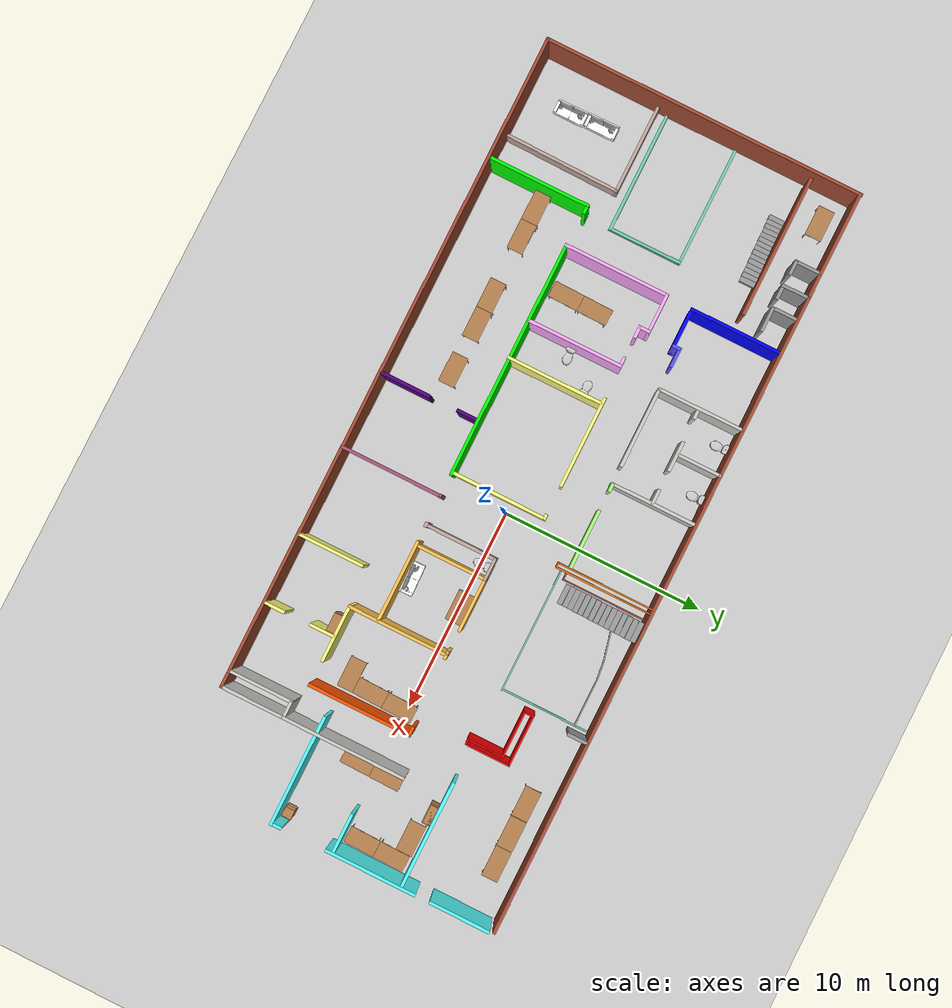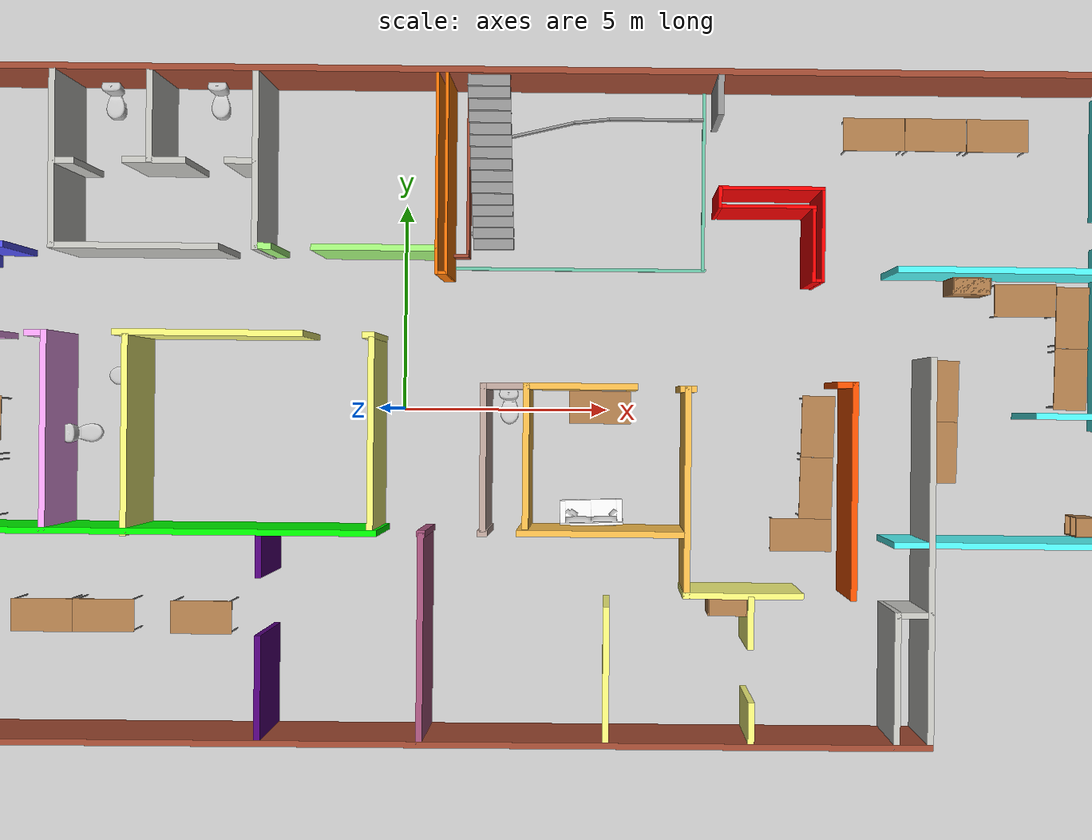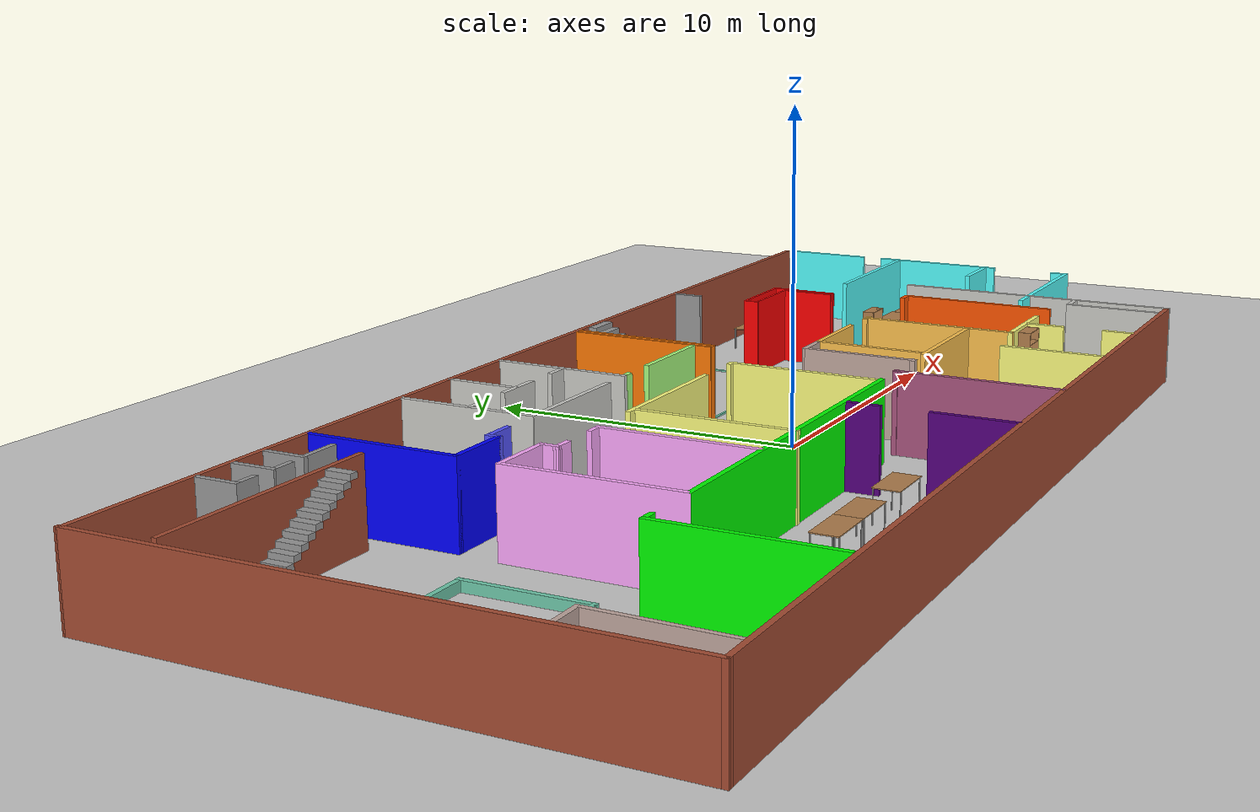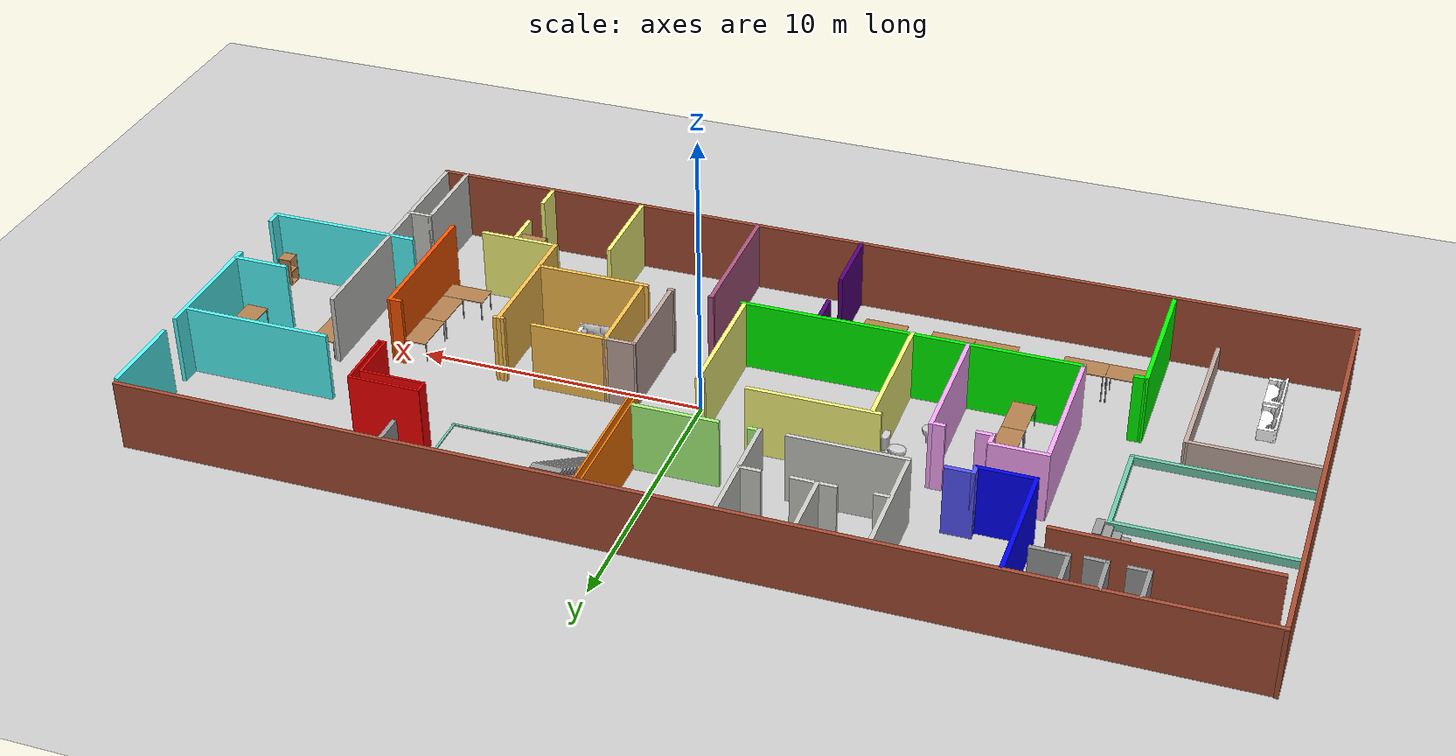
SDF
<sdf version="1.7">
 <world name="default">
  <spherical_coordinates>
   <surface_model>EARTH_WGS84</surface_model>
   <latitude_deg>6.2090793</latitude_deg>
   <longitude_deg>-75.5716712</longitude_deg>
   <elevation>0</elevation>
   <heading_deg>120</heading_deg>
  </spherical_coordinates>
  <light name="sun" type="directional">
   <pose>0 0 10 0 -0 0</pose>
   <diffuse>0.8 0.8 0.8 1</diffuse>
   <specular>0.2 0.2 0.2 1</specular>
   <attenuation>
    <range>1000</range>
    <constant>0.9</constant>
    <linear>0.01</linear>
    <quadratic>0.001</quadratic>
   </attenuation>
   <direction>-0.5 0.1 -0.9</direction>
   <spot><inner_angle>0</inner_angle><outer_angle>0</outer_angle><falloff>0</falloff></spot>
  </light>
  <model name="ground_plane">
   <static>1</static>
   <link name="link">
    <collision name="collision">
     <geometry><plane><normal>0 0 1</normal><size>100 100</size></plane></geometry>
     <surface>
      <contact><collide_bitmask>65535</collide_bitmask></contact>
      <friction><ode><mu>100</mu><mu2>50</mu2></ode></friction>
     </surface>
    </collision>
    <visual name="visual">
     <cast_shadows>0</cast_shadows>
     <geometry><plane><normal>0 0 1</normal><size>100 100</size></plane></geometry>
     <material>
      <script><uri>file://media/materials/scripts/gazebo.material</uri><name>Gazebo/Grey</name></script>
     </material>
    </visual>
   </link>
  </model>
  <gravity>0 0 -9.8</gravity>
  <magnetic_field>6e-06 2.3e-05 -4.2e-05</magnetic_field>
  <atmosphere type="adiabatic"/>
  <physics type="ode">
   <max_step_size>0.001</max_step_size>
   <real_time_factor>1</real_time_factor>
   <real_time_update_rate>1000</real_time_update_rate>
  </physics>
  <scene><ambient>0.4 0.4 0.4 1</ambient><background>0.7 0.7 0.7 1</background><shadows>1</shadows></scene>
  <spherical_coordinates>
   <surface_model>EARTH_WGS84</surface_model>
   <latitude_deg>0</latitude_deg>
   <longitude_deg>0</longitude_deg>
   <elevation>0</elevation>
   <heading_deg>0</heading_deg>
  </spherical_coordinates>
  <model name="finalfinal">
   <pose>-1.52945 0.041943 0 0 -0 0</pose>
   <link name="Stairs_0">
    <visual name="Stairs_0_Visual_0">
     <pose>-16.4011 5.10556 0.083333 0 -0 1.5708</pose>
     <geometry><box><size>0.747 0.265533 0.166667</size></box></geometry>
     <material>
      <script><uri>file://media/materials/scripts/gazebo.material</uri><name>Gazebo/Grey</name></script>
      <ambient>1 1 1 1</ambient>
     </material>
     <meta><layer>0</layer></meta>
    </visual>
    <collision name="Stairs_0_Collision_0">
     <geometry><box><size>0.747 0.265533 0.166667</size></box></geometry>
     <pose>-16.4011 5.10556 0.083333 0 -0 1.5708</pose>
    </collision>
    <visual name="Stairs_0_Visual_1">
     <pose>-16.1355 5.10556 0.25 0 -0 1.5708</pose>
     <geometry><box><size>0.747 0.265533 0.166667</size></box></geometry>
     <material>
      <script><uri>file://media/materials/scripts/gazebo.material</uri><name>Gazebo/Grey</name></script>
      <ambient>1 1 1 1</ambient>
     </material>
     <meta><layer>0</layer></meta>
    </visual>
    <collision name="Stairs_0_Collision_1">
     <geometry><box><size>0.747 0.265533 0.166667</size></box></geometry>
     <pose>-16.1355 5.10556 0.25 0 -0 1.5708</pose>
    </collision>
    <visual name="Stairs_0_Visual_2">
     <pose>-15.87 5.10556 0.416667 0 -0 1.5708</pose>
     <geometry><box><size>0.747 0.265533 0.166667</size></box></geometry>
     <material>
      <script><uri>file://media/materials/scripts/gazebo.material</uri><name>Gazebo/Grey</name></script>
      <ambient>1 1 1 1</ambient>
     </material>
     <meta><layer>0</layer></meta>
    </visual>
    <collision name="Stairs_0_Collision_2">
     <geometry><box><size>0.747 0.265533 0.166667</size></box></geometry>
     <pose>-15.87 5.10556 0.416667 0 -0 1.5708</pose>
    </collision>
    <visual name="Stairs_0_Visual_3">
     <pose>-15.6045 5.10556 0.583333 0 -0 1.5708</pose>
     <geometry><box><size>0.747 0.265533 0.166667</size></box></geometry>
     <material>
      <script><uri>file://media/materials/scripts/gazebo.material</uri><name>Gazebo/Grey</name></script>
      <ambient>1 1 1 1</ambient>
     </material>
     <meta><layer>0</layer></meta>
    </visual>
    <collision name="Stairs_0_Collision_3">
     <geometry><box><size>0.747 0.265533 0.166667</size></box></geometry>
     <pose>-15.6045 5.10556 0.583333 0 -0 1.5708</pose>
    </collision>
    <visual name="Stairs_0_Visual_4">
     <pose>-15.3389 5.10556 0.75 0 -0 1.5708</pose>
     <geometry><box><size>0.747 0.265533 0.166667</size></box></geometry>
     <material>
      <script><uri>file://media/materials/scripts/gazebo.material</uri><name>Gazebo/Grey</name></script>
      <ambient>1 1 1 1</ambient>
     </material>
     <meta><layer>0</layer></meta>
    </visual>
    <collision name="Stairs_0_Collision_4">
     <geometry><box><size>0.747 0.265533 0.166667</size></box></geometry>
     <pose>-15.3389 5.10556 0.75 0 -0 1.5708</pose>
    </collision>
    <visual name="Stairs_0_Visual_5">
     <pose>-15.0734 5.10556 0.916667 0 -0 1.5708</pose>
     <geometry><box><size>0.747 0.265533 0.166667</size></box></geometry>
     <material>
      <script><uri>file://media/materials/scripts/gazebo.material</uri><name>Gazebo/Grey</name></script>
      <ambient>1 1 1 1</ambient>
     </material>
     <meta><layer>0</layer></meta>
    </visual>
    <collision name="Stairs_0_Collision_5">
     <geometry><box><size>0.747 0.265533 0.166667</size></box></geometry>
     <pose>-15.0734 5.10556 0.916667 0 -0 1.5708</pose>
    </collision>
    <visual name="Stairs_0_Visual_6">
     <pose>-14.8079 5.10556 1.08333 0 -0 1.5708</pose>
     <geometry><box><size>0.747 0.265533 0.166667</size></box></geometry>
     <material>
      <script><uri>file://media/materials/scripts/gazebo.material</uri><name>Gazebo/Grey</name></script>
      <ambient>1 1 1 1</ambient>
     </material>
     <meta><layer>0</layer></meta>
    </visual>
    <collision name="Stairs_0_Collision_6">
     <geometry><box><size>0.747 0.265533 0.166667</size></box></geometry>
     <pose>-14.8079 5.10556 1.08333 0 -0 1.5708</pose>
    </collision>
    <visual name="Stairs_0_Visual_7">
     <pose>-14.5423 5.10556 1.25 0 -0 1.5708</pose>
     <geometry><box><size>0.747 0.265533 0.166667</size></box></geometry>
     <material>
      <script><uri>file://media/materials/scripts/gazebo.material</uri><name>Gazebo/Grey</name></script>
      <ambient>1 1 1 1</ambient>
     </material>
     <meta><layer>0</layer></meta>
    </visual>
    <collision name="Stairs_0_Collision_7">
     <geometry><box><size>0.747 0.265533 0.166667</size></box></geometry>
     <pose>-14.5423 5.10556 1.25 0 -0 1.5708</pose>
    </collision>
    <visual name="Stairs_0_Visual_8">
     <pose>-14.2768 5.10556 1.41667 0 -0 1.5708</pose>
     <geometry><box><size>0.747 0.265533 0.166667</size></box></geometry>
     <material>
      <script><uri>file://media/materials/scripts/gazebo.material</uri><name>Gazebo/Grey</name></script>
      <ambient>1 1 1 1</ambient>
     </material>
     <meta><layer>0</layer></meta>
    </visual>
    <collision name="Stairs_0_Collision_8">
     <geometry><box><size>0.747 0.265533 0.166667</size></box></geometry>
     <pose>-14.2768 5.10556 1.41667 0 -0 1.5708</pose>
    </collision>
    <visual name="Stairs_0_Visual_9">
     <pose>-14.0113 5.10556 1.58333 0 -0 1.5708</pose>
     <geometry><box><size>0.747 0.265533 0.166667</size></box></geometry>
     <material>
      <script><uri>file://media/materials/scripts/gazebo.material</uri><name>Gazebo/Grey</name></script>
      <ambient>1 1 1 1</ambient>
     </material>
     <meta><layer>0</layer></meta>
    </visual>
    <collision name="Stairs_0_Collision_9">
     <geometry><box><size>0.747 0.265533 0.166667</size></box></geometry>
     <pose>-14.0113 5.10556 1.58333 0 -0 1.5708</pose>
    </collision>
    <visual name="Stairs_0_Visual_10">
     <pose>-13.7457 5.10556 1.75 0 -0 1.5708</pose>
     <geometry><box><size>0.747 0.265533 0.166667</size></box></geometry>
     <material>
      <script><uri>file://media/materials/scripts/gazebo.material</uri><name>Gazebo/Grey</name></script>
      <ambient>1 1 1 1</ambient>
     </material>
     <meta><layer>0</layer></meta>
    </visual>
    <collision name="Stairs_0_Collision_10">
     <geometry><box><size>0.747 0.265533 0.166667</size></box></geometry>
     <pose>-13.7457 5.10556 1.75 0 -0 1.5708</pose>
    </collision>
    <visual name="Stairs_0_Visual_11">
     <pose>-13.4802 5.10556 1.91667 0 -0 1.5708</pose>
     <geometry><box><size>0.747 0.265533 0.166667</size></box></geometry>
     <material>
      <script><uri>file://media/materials/scripts/gazebo.material</uri><name>Gazebo/Grey</name></script>
      <ambient>1 1 1 1</ambient>
     </material>
     <meta><layer>0</layer></meta>
    </visual>
    <collision name="Stairs_0_Collision_11">
     <geometry><box><size>0.747 0.265533 0.166667</size></box></geometry>
     <pose>-13.4802 5.10556 1.91667 0 -0 1.5708</pose>
    </collision>
    <visual name="Stairs_0_Visual_12">
     <pose>-13.2147 5.10556 2.08333 0 -0 1.5708</pose>
     <geometry><box><size>0.747 0.265533 0.166667</size></box></geometry>
     <material>
      <script><uri>file://media/materials/scripts/gazebo.material</uri><name>Gazebo/Grey</name></script>
      <ambient>1 1 1 1</ambient>
     </material>
     <meta><layer>0</layer></meta>
    </visual>
    <collision name="Stairs_0_Collision_12">
     <geometry><box><size>0.747 0.265533 0.166667</size></box></geometry>
     <pose>-13.2147 5.10556 2.08333 0 -0 1.5708</pose>
    </collision>
    <visual name="Stairs_0_Visual_13">
     <pose>-12.9491 5.10556 2.25 0 -0 1.5708</pose>
     <geometry><box><size>0.747 0.265533 0.166667</size></box></geometry>
     <material>
      <script><uri>file://media/materials/scripts/gazebo.material</uri><name>Gazebo/Grey</name></script>
      <ambient>1 1 1 1</ambient>
     </material>
     <meta><layer>0</layer></meta>
    </visual>
    <collision name="Stairs_0_Collision_13">
     <geometry><box><size>0.747 0.265533 0.166667</size></box></geometry>
     <pose>-12.9491 5.10556 2.25 0 -0 1.5708</pose>
    </collision>
    <visual name="Stairs_0_Visual_14">
     <pose>-12.6836 5.10556 2.41667 0 -0 1.5708</pose>
     <geometry><box><size>0.747 0.265533 0.166667</size></box></geometry>
     <material>
      <script><uri>file://media/materials/scripts/gazebo.material</uri><name>Gazebo/Grey</name></script>
      <ambient>1 1 1 1</ambient>
     </material>
     <meta><layer>0</layer></meta>
    </visual>
    <collision name="Stairs_0_Collision_14">
     <geometry><box><size>0.747 0.265533 0.166667</size></box></geometry>
     <pose>-12.6836 5.10556 2.41667 0 -0 1.5708</pose>
    </collision>
   </link>
   <link name="Stairs_1">
    <visual name="Stairs_1_Visual_0">
     <pose>3.69214 4.04361 0.083333 0 -0 -3.14159</pose>
     <geometry><box><size>1 0.2592 0.166667</size></box></geometry>
     <material>
      <script><uri>file://media/materials/scripts/gazebo.material</uri><name>Gazebo/Grey</name></script>
      <ambient>1 1 1 1</ambient>
     </material>
     <meta><layer>0</layer></meta>
    </visual>
    <collision name="Stairs_1_Collision_0">
     <geometry><box><size>1 0.2592 0.166667</size></box></geometry>
     <pose>3.69214 4.04361 0.083333 0 -0 -3.14159</pose>
    </collision>
    <visual name="Stairs_1_Visual_1">
     <pose>3.69214 4.30281 0.25 0 -0 -3.14159</pose>
     <geometry><box><size>1 0.2592 0.166667</size></box></geometry>
     <material>
      <script><uri>file://media/materials/scripts/gazebo.material</uri><name>Gazebo/Grey</name></script>
      <ambient>1 1 1 1</ambient>
     </material>
     <meta><layer>0</layer></meta>
    </visual>
    <collision name="Stairs_1_Collision_1">
     <geometry><box><size>1 0.2592 0.166667</size></box></geometry>
     <pose>3.69214 4.30281 0.25 0 -0 -3.14159</pose>
    </collision>
    <visual name="Stairs_1_Visual_2">
     <pose>3.69214 4.56201 0.416667 0 -0 -3.14159</pose>
     <geometry><box><size>1 0.2592 0.166667</size></box></geometry>
     <material>
      <script><uri>file://media/materials/scripts/gazebo.material</uri><name>Gazebo/Grey</name></script>
      <ambient>1 1 1 1</ambient>
     </material>
     <meta><layer>0</layer></meta>
    </visual>
    <collision name="Stairs_1_Collision_2">
     <geometry><box><size>1 0.2592 0.166667</size></box></geometry>
     <pose>3.69214 4.56201 0.416667 0 -0 -3.14159</pose>
    </collision>
    <visual name="Stairs_1_Visual_3">
     <pose>3.69214 4.82121 0.583333 0 -0 -3.14159</pose>
     <geometry><box><size>1 0.2592 0.166667</size></box></geometry>
     <material>
      <script><uri>file://media/materials/scripts/gazebo.material</uri><name>Gazebo/Grey</name></script>
      <ambient>1 1 1 1</ambient>
     </material>
     <meta><layer>0</layer></meta>
    </visual>
    <collision name="Stairs_1_Collision_3">
     <geometry><box><size>1 0.2592 0.166667</size></box></geometry>
     <pose>3.69214 4.82121 0.583333 0 -0 -3.14159</pose>
    </collision>
    <visual name="Stairs_1_Visual_4">
     <pose>3.69214 5.08042 0.75 0 -0 -3.14159</pose>
     <geometry><box><size>1 0.2592 0.166667</size></box></geometry>
     <material>
      <script><uri>file://media/materials/scripts/gazebo.material</uri><name>Gazebo/Grey</name></script>
      <ambient>1 1 1 1</ambient>
     </material>
     <meta><layer>0</layer></meta>
    </visual>
    <collision name="Stairs_1_Collision_4">
     <geometry><box><size>1 0.2592 0.166667</size></box></geometry>
     <pose>3.69214 5.08042 0.75 0 -0 -3.14159</pose>
    </collision>
    <visual name="Stairs_1_Visual_5">
     <pose>3.69214 5.33962 0.916667 0 -0 -3.14159</pose>
     <geometry><box><size>1 0.2592 0.166667</size></box></geometry>
     <material>
      <script><uri>file://media/materials/scripts/gazebo.material</uri><name>Gazebo/Grey</name></script>
      <ambient>1 1 1 1</ambient>
     </material>
     <meta><layer>0</layer></meta>
    </visual>
    <collision name="Stairs_1_Collision_5">
     <geometry><box><size>1 0.2592 0.166667</size></box></geometry>
     <pose>3.69214 5.33962 0.916667 0 -0 -3.14159</pose>
    </collision>
    <visual name="Stairs_1_Visual_6">
     <pose>3.69214 5.59882 1.08333 0 -0 -3.14159</pose>
     <geometry><box><size>1 0.2592 0.166667</size></box></geometry>
     <material>
      <script><uri>file://media/materials/scripts/gazebo.material</uri><name>Gazebo/Grey</name></script>
      <ambient>1 1 1 1</ambient>
     </material>
     <meta><layer>0</layer></meta>
    </visual>
    <collision name="Stairs_1_Collision_6">
     <geometry><box><size>1 0.2592 0.166667</size></box></geometry>
     <pose>3.69214 5.59882 1.08333 0 -0 -3.14159</pose>
    </collision>
    <visual name="Stairs_1_Visual_7">
     <pose>3.69214 5.85801 1.25 0 -0 -3.14159</pose>
     <geometry><box><size>1 0.2592 0.166667</size></box></geometry>
     <material>
      <script><uri>file://media/materials/scripts/gazebo.material</uri><name>Gazebo/Grey</name></script>
      <ambient>1 1 1 1</ambient>
     </material>
     <meta><layer>0</layer></meta>
    </visual>
    <collision name="Stairs_1_Collision_7">
     <geometry><box><size>1 0.2592 0.166667</size></box></geometry>
     <pose>3.69214 5.85801 1.25 0 -0 -3.14159</pose>
    </collision>
    <visual name="Stairs_1_Visual_8">
     <pose>3.69214 6.11721 1.41667 0 -0 -3.14159</pose>
     <geometry><box><size>1 0.2592 0.166667</size></box></geometry>
     <material>
      <script><uri>file://media/materials/scripts/gazebo.material</uri><name>Gazebo/Grey</name></script>
      <ambient>1 1 1 1</ambient>
     </material>
     <meta><layer>0</layer></meta>
    </visual>
    <collision name="Stairs_1_Collision_8">
     <geometry><box><size>1 0.2592 0.166667</size></box></geometry>
     <pose>3.69214 6.11721 1.41667 0 -0 -3.14159</pose>
    </collision>
    <visual name="Stairs_1_Visual_9">
     <pose>3.69214 6.37641 1.58333 0 -0 -3.14159</pose>
     <geometry><box><size>1 0.2592 0.166667</size></box></geometry>
     <material>
      <script><uri>file://media/materials/scripts/gazebo.material</uri><name>Gazebo/Grey</name></script>
      <ambient>1 1 1 1</ambient>
     </material>
     <meta><layer>0</layer></meta>
    </visual>
    <collision name="Stairs_1_Collision_9">
     <geometry><box><size>1 0.2592 0.166667</size></box></geometry>
     <pose>3.69214 6.37641 1.58333 0 -0 -3.14159</pose>
    </collision>
    <visual name="Stairs_1_Visual_10">
     <pose>3.69214 6.63561 1.75 0 -0 -3.14159</pose>
     <geometry><box><size>1 0.2592 0.166667</size></box></geometry>
     <material>
      <script><uri>file://media/materials/scripts/gazebo.material</uri><name>Gazebo/Grey</name></script>
      <ambient>1 1 1 1</ambient>
     </material>
     <meta><layer>0</layer></meta>
    </visual>
    <collision name="Stairs_1_Collision_10">
     <geometry><box><size>1 0.2592 0.166667</size></box></geometry>
     <pose>3.69214 6.63561 1.75 0 -0 -3.14159</pose>
    </collision>
    <visual name="Stairs_1_Visual_11">
     <pose>3.69214 6.89482 1.91667 0 -0 -3.14159</pose>
     <geometry><box><size>1 0.2592 0.166667</size></box></geometry>
     <material>
      <script><uri>file://media/materials/scripts/gazebo.material</uri><name>Gazebo/Grey</name></script>
      <ambient>1 1 1 1</ambient>
     </material>
     <meta><layer>0</layer></meta>
    </visual>
    <collision name="Stairs_1_Collision_11">
     <geometry><box><size>1 0.2592 0.166667</size></box></geometry>
     <pose>3.69214 6.89482 1.91667 0 -0 -3.14159</pose>
    </collision>
    <visual name="Stairs_1_Visual_12">
     <pose>3.69214 7.15402 2.08333 0 -0 -3.14159</pose>
     <geometry><box><size>1 0.2592 0.166667</size></box></geometry>
     <material>
      <script><uri>file://media/materials/scripts/gazebo.material</uri><name>Gazebo/Grey</name></script>
      <ambient>1 1 1 1</ambient>
     </material>
     <meta><layer>0</layer></meta>
    </visual>
    <collision name="Stairs_1_Collision_12">
     <geometry><box><size>1 0.2592 0.166667</size></box></geometry>
     <pose>3.69214 7.15402 2.08333 0 -0 -3.14159</pose>
    </collision>
    <visual name="Stairs_1_Visual_13">
     <pose>3.69214 7.41322 2.25 0 -0 -3.14159</pose>
     <geometry><box><size>1 0.2592 0.166667</size></box></geometry>
     <material>
      <script><uri>file://media/materials/scripts/gazebo.material</uri><name>Gazebo/Grey</name></script>
      <ambient>1 1 1 1</ambient>
     </material>
     <meta><layer>0</layer></meta>
    </visual>
    <collision name="Stairs_1_Collision_13">
     <geometry><box><size>1 0.2592 0.166667</size></box></geometry>
     <pose>3.69214 7.41322 2.25 0 -0 -3.14159</pose>
    </collision>
    <visual name="Stairs_1_Visual_14">
     <pose>3.69214 7.67241 2.41667 0 -0 -3.14159</pose>
     <geometry><box><size>1 0.2592 0.166667</size></box></geometry>
     <material>
      <script><uri>file://media/materials/scripts/gazebo.material</uri><name>Gazebo/Grey</name></script>
      <ambient>1 1 1 1</ambient>
     </material>
     <meta><layer>0</layer></meta>
    </visual>
    <collision name="Stairs_1_Collision_14">
     <geometry><box><size>1 0.2592 0.166667</size></box></geometry>
     <pose>3.69214 7.67241 2.41667 0 -0 -3.14159</pose>
    </collision>
   </link>
   <link name="Wall_0">
    <collision name="Wall_0_Collision">
     <geometry><box><size>37.14 0.15 2.5</size></box></geometry>
     <pose>0 0 1.25 0 -0 0</pose>
    </collision>
    <visual name="Wall_0_Visual">
     <pose>0 0 1.25 0 -0 0</pose>
     <geometry><box><size>37.14 0.15 2.5</size></box></geometry>
     <material>
      <script><uri>file://media/materials/scripts/gazebo.material</uri><name>Gazebo/Bricks</name></script>
      <ambient>1 1 1 1</ambient>
     </material>
     <meta><layer>0</layer></meta>
    </visual>
    <pose>-0.072531 7.91705 0 0 -0 0</pose>
   </link>
   <link name="Wall_101">
    <collision name="Wall_101_Collision">
     <geometry><box><size>0.39 0.07 0.7</size></box></geometry>
     <pose>0 0 0.35 0 -0 0</pose>
    </collision>
    <visual name="Wall_101_Visual">
     <pose>0 0 0.35 0 -0 0</pose>
     <geometry><box><size>0.39 0.07 0.7</size></box></geometry>
     <material>
      <script><uri>file://media/materials/scripts/gazebo.material</uri><name>Gazebo/Bricks</name></script>
      <ambient>1 1 1 1</ambient>
     </material>
     <meta><layer>0</layer></meta>
    </visual>
    <pose>2.93345 3.70306 0 0 -0 0</pose>
   </link>
   <link name="Wall_103">
    <collision name="Wall_103_Collision">
     <geometry><box><size>4.25 0.07 0.7</size></box></geometry>
     <pose>0 0 0.35 0 -0 0</pose>
    </collision>
    <visual name="Wall_103_Visual">
     <pose>0 0 0.35 0 -0 0</pose>
     <geometry><box><size>4.25 0.07 0.7</size></box></geometry>
     <material>
      <script><uri>file://media/materials/scripts/gazebo.material</uri><name>Gazebo/Bricks</name></script>
      <ambient>1 1 1 1</ambient>
     </material>
     <meta><layer>0</layer></meta>
    </visual>
    <pose>3.09345 5.79306 0 0 -0 1.5708</pose>
   </link>
   <link name="Wall_105">
    <collision name="Wall_105_Collision">
     <geometry><box><size>1 0.15 2.5</size></box></geometry>
     <pose>0 0 1.25 0 -0 0</pose>
    </collision>
    <visual name="Wall_105_Visual">
     <pose>0 0 1.25 0 -0 0</pose>
     <geometry><box><size>1 0.15 2.5</size></box></geometry>
     <material>
      <script><uri>file://media/materials/scripts/gazebo.material</uri><name>Gazebo/Grey</name></script>
      <ambient>1 1 1 1</ambient>
     </material>
     <meta><layer>0</layer></meta>
    </visual>
    <pose>9.13765 7.40657 0 0 -0 -1.5708</pose>
   </link>
   <link name="Wall_113">
    <collision name="Wall_113_Collision">
     <geometry><box><size>0.5 0.08 2.5</size></box></geometry>
     <pose>0 0 1.25 0 -0 0</pose>
    </collision>
    <visual name="Wall_113_Visual">
     <pose>0 0 1.25 0 -0 0</pose>
     <geometry><box><size>0.5 0.08 2.5</size></box></geometry>
     <material>
      <script><uri>file://media/materials/scripts/gazebo.material</uri><name>Gazebo/Grey</name></script>
      <ambient>1 0 0 1</ambient>
     </material>
     <meta><layer>0</layer></meta>
    </visual>
    <pose>9.14236 4.97184 0 0 -0 1.5708</pose>
   </link>
   <link name="Wall_115">
    <collision name="Wall_115_Collision">
     <geometry><box><size>2.5 0.08 2.5</size></box></geometry>
     <pose>0 0 1.25 0 -0 0</pose>
    </collision>
    <visual name="Wall_115_Visual">
     <pose>0 0 1.25 0 -0 0</pose>
     <geometry><box><size>2.5 0.08 2.5</size></box></geometry>
     <material>
      <script><uri>file://media/materials/scripts/gazebo.material</uri><name>Gazebo/Grey</name></script>
      <ambient>1 0 0 1</ambient>
     </material>
     <meta><layer>0</layer></meta>
    </visual>
    <pose>10.3562 5.20204 0 0 -0 0</pose>
   </link>
   <link name="Wall_119">
    <collision name="Wall_119_Collision">
     <geometry><box><size>2.25 0.08 2.5</size></box></geometry>
     <pose>0 0 1.25 0 -0 0</pose>
    </collision>
    <visual name="Wall_119_Visual">
     <pose>0 0 1.25 0 -0 0</pose>
     <geometry><box><size>2.25 0.08 2.5</size></box></geometry>
     <material>
      <script><uri>file://media/materials/scripts/gazebo.material</uri><name>Gazebo/Grey</name></script>
      <ambient>1 0 0 1</ambient>
     </material>
     <meta><layer>0</layer></meta>
    </visual>
    <pose>10.2699 4.7714 0 0 -0 0</pose>
   </link>
   <link name="Wall_129">
    <collision name="Wall_129_Collision">
     <geometry><box><size>4.5 0.08 0.05</size></box></geometry>
     <pose>0 0 0.025 0 -0 0</pose>
    </collision>
    <visual name="Wall_129_Visual">
     <pose>0 0 0.025 0 -0 0</pose>
     <geometry><box><size>4.5 0.08 0.05</size></box></geometry>
     <material>
      <script><uri>file://media/materials/scripts/gazebo.material</uri><name>Gazebo/Grey</name></script>
      <ambient>0.435294 0.796078 0.67451 1</ambient>
     </material>
     <meta><layer>0</layer></meta>
    </visual>
    <pose>8.88409 5.6843 0 0 -0 -1.5708</pose>
   </link>
   <link name="Wall_131">
    <collision name="Wall_131_Collision">
     <geometry><box><size>6.2 0.08 0.05</size></box></geometry>
     <pose>0 0 0.025 0 -0 0</pose>
    </collision>
    <visual name="Wall_131_Visual">
     <pose>0 0 0.025 0 -0 0</pose>
     <geometry><box><size>6.2 0.08 0.05</size></box></geometry>
     <material>
      <script><uri>file://media/materials/scripts/gazebo.material</uri><name>Gazebo/Grey</name></script>
      <ambient>0.435294 0.796078 0.67451 1</ambient>
     </material>
     <meta><layer>0</layer></meta>
    </visual>
    <pose>5.85445 3.44206 0 0 -0 0</pose>
   </link>
   <link name="Wall_133">
    <collision name="Wall_133_Collision">
     <geometry><box><size>0.35 0.07 0.2</size></box></geometry>
     <pose>0 0 0.1 0 -0 0</pose>
    </collision>
    <visual name="Wall_133_Visual">
     <pose>0 0 0.1 0 -0 0</pose>
     <geometry><box><size>0.35 0.07 0.2</size></box></geometry>
     <material>
      <script><uri>file://media/materials/scripts/gazebo.material</uri><name>Gazebo/Grey</name></script>
      <ambient>1 1 1 1</ambient>
     </material>
     <meta><layer>0</layer></meta>
    </visual>
    <pose>8.68868 7.17206 0 0 -0 3.14159</pose>
   </link>
   <link name="Wall_134">
    <collision name="Wall_134_Collision">
     <geometry><box><size>2.06434 0.06 0.2</size></box></geometry>
     <pose>0 0 0.1 0 -0 0</pose>
    </collision>
    <visual name="Wall_134_Visual">
     <pose>0 0 0.1 0 -0 0</pose>
     <geometry><box><size>2.06434 0.06 0.2</size></box></geometry>
     <material>
      <script><uri>file://media/materials/scripts/gazebo.material</uri><name>Gazebo/Grey</name></script>
      <ambient>1 1 1 1</ambient>
     </material>
     <meta><layer>0</layer></meta>
    </visual>
    <pose>7.55062 7.17206 0 0 -0 3.14159</pose>
   </link>
   <link name="Wall_135">
    <collision name="Wall_135_Collision">
     <geometry><box><size>0.942866 0.06 0.2</size></box></geometry>
     <pose>0 0 0.1 0 -0 0</pose>
    </collision>
    <visual name="Wall_135_Visual">
     <pose>0 0 0.1 0 -0 0</pose>
     <geometry><box><size>0.942866 0.06 0.2</size></box></geometry>
     <material>
      <script><uri>file://media/materials/scripts/gazebo.material</uri><name>Gazebo/Grey</name></script>
      <ambient>1 1 1 1</ambient>
     </material>
     <meta><layer>0</layer></meta>
    </visual>
    <pose>6.10945 7.12456 0 0 -0 -3.03381</pose>
   </link>
   <link name="Wall_136">
    <collision name="Wall_136_Collision">
     <geometry><box><size>2.01942 0.06 0.2</size></box></geometry>
     <pose>0 0 0.1 0 -0 0</pose>
    </collision>
    <visual name="Wall_136_Visual">
     <pose>0 0 0.1 0 -0 0</pose>
     <geometry><box><size>2.01942 0.06 0.2</size></box></geometry>
     <material>
      <script><uri>file://media/materials/scripts/gazebo.material</uri><name>Gazebo/Grey</name></script>
      <ambient>1 1 1 1</ambient>
     </material>
     <meta><layer>0</layer></meta>
    </visual>
    <pose>4.71645 6.85406 0 0 -0 -2.91196</pose>
   </link>
   <link name="Wall_138">
    <collision name="Wall_138_Collision">
     <geometry><box><size>2.38821 0.07 0.2</size></box></geometry>
     <pose>0 0 0.1 0 -0 0</pose>
    </collision>
    <visual name="Wall_138_Visual">
     <pose>0 0 0.1 0 -0 0</pose>
     <geometry><box><size>2.38821 0.07 0.2</size></box></geometry>
     <material>
      <script><uri>file://media/materials/scripts/gazebo.material</uri><name>Gazebo/Grey</name></script>
      <ambient>1 1 1 1</ambient>
     </material>
     <meta><layer>0</layer></meta>
    </visual>
    <pose>3.76245 5.47195 0 0 -0 -1.5708</pose>
   </link>
   <link name="Wall_140">
    <collision name="Wall_140_Collision">
     <geometry><box><size>0.67 0.07 0.2</size></box></geometry>
     <pose>0 0 0.1 0 -0 0</pose>
    </collision>
    <visual name="Wall_140_Visual">
     <pose>0 0 0.1 0 -0 0</pose>
     <geometry><box><size>0.67 0.07 0.2</size></box></geometry>
     <material>
      <script><uri>file://media/materials/scripts/gazebo.material</uri><name>Gazebo/Grey</name></script>
      <ambient>1 1 1 1</ambient>
     </material>
     <meta><layer>0</layer></meta>
    </visual>
    <pose>3.46245 4.30167 0 0 -0 3.14159</pose>
   </link>
   <link name="Wall_142">
    <collision name="Wall_142_Collision">
     <geometry><box><size>5 0.15 2.5</size></box></geometry>
     <pose>0 0 1.25 0 -0 0</pose>
    </collision>
    <visual name="Wall_142_Visual">
     <pose>0 0 1.25 0 -0 0</pose>
     <geometry><box><size>5 0.15 2.5</size></box></geometry>
     <material>
      <script><uri>file://media/materials/scripts/gazebo.material</uri><name>Gazebo/Grey</name></script>
      <ambient>0 1 0 1</ambient>
     </material>
     <meta><layer>0</layer></meta>
    </visual>
    <pose>-12.5694 -5.35027 0 0 -0 1.5708</pose>
   </link>
   <link name="Wall_144">
    <collision name="Wall_144_Collision">
     <geometry><box><size>0.5 0.15 2.5</size></box></geometry>
     <pose>0 0 1.25 0 -0 0</pose>
    </collision>
    <visual name="Wall_144_Visual">
     <pose>0 0 1.25 0 -0 0</pose>
     <geometry><box><size>0.5 0.15 2.5</size></box></geometry>
     <material>
      <script><uri>file://media/materials/scripts/gazebo.material</uri><name>Gazebo/Grey</name></script>
      <ambient>0 1 0 1</ambient>
     </material>
     <meta><layer>0</layer></meta>
    </visual>
    <pose>-12.3944 -2.92527 0 0 -0 0</pose>
   </link>
   <link name="Wall_146">
    <collision name="Wall_146_Collision">
     <geometry><box><size>5.4 0.15 2.5</size></box></geometry>
     <pose>0 0 1.25 0 -0 0</pose>
    </collision>
    <visual name="Wall_146_Visual">
     <pose>0 0 1.25 0 -0 0</pose>
     <geometry><box><size>5.4 0.15 2.5</size></box></geometry>
     <material>
      <script><uri>file://media/materials/scripts/gazebo.material</uri><name>Gazebo/Grey</name></script>
      <ambient>0.333333 1 1 1</ambient>
     </material>
     <meta><layer>0</layer></meta>
    </visual>
    <pose>15.9871 -3.13858 0 0 -0 0</pose>
   </link>
   <link name="Wall_15">
    <collision name="Wall_15_Collision">
     <geometry><box><size>6.14079 0.15 0.3</size></box></geometry>
     <pose>0 0 0.15 0 -0 0</pose>
    </collision>
    <visual name="Wall_15_Visual">
     <pose>0 0 0.15 0 -0 0</pose>
     <geometry><box><size>6.14079 0.15 0.3</size></box></geometry>
     <material>
      <script><uri>file://media/materials/scripts/gazebo.material</uri><name>Gazebo/Grey</name></script>
      <ambient>0.435294 0.796078 0.67451 1</ambient>
     </material>
     <meta><layer>0</layer></meta>
    </visual>
    <pose>-15.5451 -1.65394 0 0 -0 0</pose>
   </link>
   <link name="Wall_151">
    <collision name="Wall_151_Collision">
     <geometry><box><size>3.25 0.15 2.5</size></box></geometry>
     <pose>0 0 1.25 0 -0 0</pose>
    </collision>
    <visual name="Wall_151_Visual">
     <pose>0 0 1.25 0 -0 0</pose>
     <geometry><box><size>3.25 0.15 2.5</size></box></geometry>
     <material>
      <script><uri>file://media/materials/scripts/gazebo.material</uri><name>Gazebo/CeilingTiled</name></script>
      <ambient>1 0.333333 0 1</ambient>
     </material>
     <meta><layer>0</layer></meta>
    </visual>
    <pose>13.3962 -6.33688 0 0 -0 -1.5708</pose>
   </link>
   <link name="Wall_154">
    <collision name="Wall_154_Collision">
     <geometry><box><size>0.9 0.15 2.5</size></box></geometry>
     <pose>0 0 1.25 0 -0 0</pose>
    </collision>
    <visual name="Wall_154_Visual">
     <pose>0 0 1.25 0 -0 0</pose>
     <geometry><box><size>0.9 0.15 2.5</size></box></geometry>
     <material>
      <script><uri>file://media/materials/scripts/gazebo.material</uri><name>Gazebo/CeilingTiled</name></script>
      <ambient>1 0.333333 0 1</ambient>
     </material>
     <meta><layer>0</layer></meta>
    </visual>
    <pose>13.806 -4.78688 0 0 -0 0</pose>
   </link>
   <link name="Wall_156">
    <collision name="Wall_156_Collision">
     <geometry><box><size>3.5 0.15 2.5</size></box></geometry>
     <pose>0 0 1.25 0 -0 0</pose>
    </collision>
    <visual name="Wall_156_Visual">
     <pose>0 0 1.25 0 -0 0</pose>
     <geometry><box><size>3 0.15 2.5</size></box></geometry>
     <material>
      <script><uri>file://media/materials/scripts/gazebo.material</uri><name>Gazebo/Grey</name></script>
      <ambient>0.333333 1 1 1</ambient>
     </material>
     <meta><layer>0</layer></meta>
    </visual>
    <pose>18.531 6.22698 0 0 -0 -1.5708</pose>
   </link>
   <link name="Wall_158">
    <collision name="Wall_158_Collision">
     <geometry><box><size>4.5 0.15 2.5</size></box></geometry>
     <pose>0 0 1.25 0 -0 0</pose>
    </collision>
    <visual name="Wall_158_Visual">
     <pose>0 0 1.25 0 -0 0</pose>
     <geometry><box><size>4.5 0.15 2.5</size></box></geometry>
     <material>
      <script><uri>file://media/materials/scripts/gazebo.material</uri><name>Gazebo/Grey</name></script>
      <ambient>0.333333 1 1 1</ambient>
     </material>
     <meta><layer>0</layer></meta>
    </visual>
    <pose>18.5588 1.79182 0 0 -0 -1.5708</pose>
   </link>
   <link name="Wall_16">
    <collision name="Wall_16_Collision">
     <geometry><box><size>3.75 0.15 0.3</size></box></geometry>
     <pose>0 0 0.15 0 -0 0</pose>
    </collision>
    <visual name="Wall_16_Visual">
     <pose>0 0 0.15 0 -0 0</pose>
     <geometry><box><size>3.75 0.15 0.3</size></box></geometry>
     <material>
      <script><uri>file://media/materials/scripts/gazebo.material</uri><name>Gazebo/Grey</name></script>
      <ambient>0.435294 0.796078 0.67451 1</ambient>
     </material>
     <meta><layer>0</layer></meta>
    </visual>
    <pose>-12.5496 0.146057 0 0 -0 1.5708</pose>
   </link>
   <link name="Wall_162">
    <collision name="Wall_162_Collision">
     <geometry><box><size>5.18 0.15 2.5</size></box></geometry>
     <pose>0 0 1.25 0 -0 0</pose>
    </collision>
    <visual name="Wall_162_Visual">
     <pose>0 0 1.25 0 -0 0</pose>
     <geometry><box><size>5.18 0.15 2.5</size></box></geometry>
     <material>
      <script><uri>file://media/materials/scripts/gazebo.material</uri><name>Gazebo/Grey</name></script>
      <ambient>0.333333 1 1 1</ambient>
     </material>
     <meta><layer>0</layer></meta>
    </visual>
    <pose>15.9115 3.32497 0 0 -0 3.13784</pose>
   </link>
   <link name="Wall_17">
    <collision name="Wall_17_Collision">
     <geometry><box><size>6 0.15 0.3</size></box></geometry>
     <pose>0 0 0.15 0 -0 0</pose>
    </collision>
    <visual name="Wall_17_Visual">
     <pose>0 0 0.15 0 -0 0</pose>
     <geometry><box><size>6 0.15 0.3</size></box></geometry>
     <material>
      <script><uri>file://media/materials/scripts/gazebo.material</uri><name>Gazebo/Grey</name></script>
      <ambient>0.435294 0.796078 0.67451 1</ambient>
     </material>
     <meta><layer>0</layer></meta>
    </visual>
    <pose>-15.4746 1.94606 0 0 -0 3.14159</pose>
   </link>
   <link name="Wall_170">
    <collision name="Wall_170_Collision">
     <geometry><box><size>1.8 0.08 2.5</size></box></geometry>
     <pose>0 0 1.25 0 -0 0</pose>
    </collision>
    <visual name="Wall_170_Visual">
     <pose>0 0 1.25 0 -0 0</pose>
     <geometry><box><size>1.8 0.08 2.5</size></box></geometry>
     <material>
      <script><uri>file://media/materials/scripts/gazebo.material</uri><name>Gazebo/Grey</name></script>
      <ambient>1 0 0 1</ambient>
     </material>
     <meta><layer>0</layer></meta>
    </visual>
    <pose>11.3522 3.911 0 0 -0 -1.5708</pose>
   </link>
   <link name="Wall_172">
    <collision name="Wall_172_Collision">
     <geometry><box><size>2.23 0.08 2.5</size></box></geometry>
     <pose>0 0 1.25 0 -0 0</pose>
    </collision>
    <visual name="Wall_172_Visual">
     <pose>0 0 1.25 0 -0 0</pose>
     <geometry><box><size>2.23 0.08 2.5</size></box></geometry>
     <material>
      <script><uri>file://media/materials/scripts/gazebo.material</uri><name>Gazebo/Grey</name></script>
      <ambient>1 0 0 1</ambient>
     </material>
     <meta><layer>0</layer></meta>
    </visual>
    <pose>11.5668 4.11953 0 0 -0 -1.5708</pose>
   </link>
   <link name="Wall_174">
    <collision name="Wall_174_Collision">
     <geometry><box><size>0.28 0.08 2.5</size></box></geometry>
     <pose>0 0 1.25 0 -0 0</pose>
    </collision>
    <visual name="Wall_174_Visual">
     <pose>0 0 1.25 0 -0 0</pose>
     <geometry><box><size>0.28 0.08 2.5</size></box></geometry>
     <material>
      <script><uri>file://media/materials/scripts/gazebo.material</uri><name>Gazebo/Grey</name></script>
      <ambient>1 0 0 1</ambient>
     </material>
     <meta><layer>0</layer></meta>
    </visual>
    <pose>11.4569 3.04845 0 0 -0 0</pose>
   </link>
   <link name="Wall_178">
    <collision name="Wall_178_Collision">
     <geometry><box><size>2 0.15 2.5</size></box></geometry>
     <pose>0 0 1.25 0 -0 0</pose>
    </collision>
    <visual name="Wall_178_Visual">
     <pose>0 0 1.25 0 -0 0</pose>
     <geometry><box><size>2 0.15 2.5</size></box></geometry>
     <material>
      <script><uri>file://media/materials/scripts/gazebo.material</uri><name>Gazebo/Grey</name></script>
      <ambient>0.333333 1 1 1</ambient>
     </material>
     <meta><layer>0</layer></meta>
    </visual>
    <pose>17.5971 -0.088137 0 0 -0 0</pose>
   </link>
   <link name="Wall_180">
    <collision name="Wall_180_Collision">
     <geometry><box><size>0.5 0.15 2.5</size></box></geometry>
     <pose>0 0 1.25 0 -0 0</pose>
    </collision>
    <visual name="Wall_180_Visual">
     <pose>0 0 1.25 0 -0 0</pose>
     <geometry><box><size>0.5 0.15 2.5</size></box></geometry>
     <material>
      <script><uri>file://media/materials/scripts/gazebo.material</uri><name>Gazebo/Grey</name></script>
      <ambient>0.333333 1 1 1</ambient>
     </material>
     <meta><layer>0</layer></meta>
    </visual>
    <pose>18.594 -2.85834 0 0 -0 -1.5708</pose>
   </link>
   <link name="Wall_19">
    <collision name="Wall_19_Collision">
     <geometry><box><size>7 0.15 2.5</size></box></geometry>
     <pose>0 0 1.25 0 -0 0</pose>
    </collision>
    <visual name="Wall_19_Visual">
     <pose>0 0 1.25 0 -0 0</pose>
     <geometry><box><size>7 0.15 2.5</size></box></geometry>
     <material>
      <script><uri>file://media/materials/scripts/gazebo.material</uri><name>Gazebo/Bricks</name></script>
      <ambient>1 1 1 1</ambient>
     </material>
     <meta><layer>0</layer></meta>
    </visual>
    <pose>-14.7516 5.60406 0 0 -0 0</pose>
   </link>
   <link name="Wall_193">
    <collision name="Wall_193_Collision">
     <geometry><box><size>4.75 0.15 2.5</size></box></geometry>
     <pose>0 0 1.25 0 -0 0</pose>
    </collision>
    <visual name="Wall_193_Visual">
     <pose>0 0 1.25 0 -0 0</pose>
     <geometry><box><size>4.75 0.15 2.5</size></box></geometry>
     <material>
      <script><uri>file://media/materials/scripts/gazebo.material</uri><name>Gazebo/Grey</name></script>
      <ambient>1 1 0.498039 1</ambient>
     </material>
     <meta><layer>0</layer></meta>
    </visual>
    <pose>-4.78968 -0.712961 0 0 -0 1.5708</pose>
   </link>
   <link name="Wall_195">
    <collision name="Wall_195_Collision">
     <geometry><box><size>4.5 0.15 2.5</size></box></geometry>
     <pose>0 0 1.25 0 -0 0</pose>
    </collision>
    <visual name="Wall_195_Visual">
     <pose>0 0 1.25 0 -0 0</pose>
     <geometry><box><size>4.5 0.15 2.5</size></box></geometry>
     <material>
      <script><uri>file://media/materials/scripts/gazebo.material</uri><name>Gazebo/Grey</name></script>
      <ambient>1 1 0.498039 1</ambient>
     </material>
     <meta><layer>0</layer></meta>
    </visual>
    <pose>-2.85714 1.69353 0 0 -0 0</pose>
   </link>
   <link name="Wall_2">
    <collision name="Wall_2_Collision">
     <geometry><box><size>16.0748 0.15 2.5</size></box></geometry>
     <pose>0 0 1.25 0 -0 0</pose>
    </collision>
    <visual name="Wall_2_Visual">
     <pose>0 0 1.25 0 -0 0</pose>
     <geometry><box><size>16.0748 0.15 2.5</size></box></geometry>
     <material>
      <script><uri>file://media/materials/scripts/gazebo.material</uri><name>Gazebo/Bricks</name></script>
      <ambient>1 1 1 1</ambient>
     </material>
     <meta><layer>0</layer></meta>
    </visual>
    <pose>-18.5896 -0 0 0 -0 -1.57357</pose>
   </link>
   <link name="Wall_201">
    <collision name="Wall_201_Collision">
     <geometry><box><size>4.6 0.15 2.5</size></box></geometry>
     <pose>0 0 1.25 0 -0 0</pose>
    </collision>
    <visual name="Wall_201_Visual">
     <pose>0 0 1.25 0 -0 0</pose>
     <geometry><box><size>4.6 0.15 2.5</size></box></geometry>
     <material>
      <script><uri>file://media/materials/scripts/gazebo.material</uri><name>Gazebo/Grey</name></script>
      <ambient>1 1 0.498039 1</ambient>
     </material>
     <meta><layer>0</layer></meta>
    </visual>
    <pose>0.991225 -0.671862 0 0 -0 1.5708</pose>
   </link>
   <link name="Wall_207">
    <collision name="Wall_207_Collision">
     <geometry><box><size>0.4 0.15 2.5</size></box></geometry>
     <pose>0 0 1.25 0 -0 0</pose>
    </collision>
    <visual name="Wall_207_Visual">
     <pose>0 0 1.25 0 -0 0</pose>
     <geometry><box><size>0.4 0.15 2.5</size></box></geometry>
     <material>
      <script><uri>file://media/materials/scripts/gazebo.material</uri><name>Gazebo/Grey</name></script>
      <ambient>1 0.666667 1 1</ambient>
     </material>
     <meta><layer>0</layer></meta>
    </visual>
    <pose>-6.95721 1.65482 0 0 -0 0</pose>
   </link>
   <link name="Wall_21">
    <collision name="Wall_21_Collision">
     <geometry><box><size>1.34125 0.15 2.5</size></box></geometry>
     <pose>0 0 1.25 0 -0 0</pose>
    </collision>
    <visual name="Wall_21_Visual">
     <pose>0 0 1.25 0 -0 0</pose>
     <geometry><box><size>1.34125 0.15 2.5</size></box></geometry>
     <material>
      <script><uri>file://media/materials/scripts/gazebo.material</uri><name>Gazebo/Grey</name></script>
      <ambient>1 1 1 1</ambient>
     </material>
     <meta><layer>0</layer></meta>
    </visual>
    <pose>-14.509 7.26554 0 0 -0 -1.5708</pose>
   </link>
   <link name="Wall_216">
    <collision name="Wall_216_Collision">
     <geometry><box><size>1.25 0.15 2.5</size></box></geometry>
     <pose>0 0 1.25 0 -0 0</pose>
    </collision>
    <visual name="Wall_216_Visual">
     <pose>0 0 1.25 0 -0 0</pose>
     <geometry><box><size>1.25 0.15 2.5</size></box></geometry>
     <material>
      <script><uri>file://media/materials/scripts/gazebo.material</uri><name>Gazebo/Grey</name></script>
      <ambient>1 1 0.498039 1</ambient>
     </material>
     <meta><layer>0</layer></meta>
    </visual>
    <pose>9.94867 -5.00705 0 0 -0 -1.5708</pose>
   </link>
   <link name="Wall_218">
    <collision name="Wall_218_Collision">
     <geometry><box><size>1 0.15 2.5</size></box></geometry>
     <pose>0 0 1.25 0 -0 0</pose>
    </collision>
    <visual name="Wall_218_Visual">
     <pose>0 0 1.25 0 -0 0</pose>
     <geometry><box><size>1 0.15 2.5</size></box></geometry>
     <material>
      <script><uri>file://media/materials/scripts/gazebo.material</uri><name>Gazebo/Grey</name></script>
      <ambient>1 1 0.498039 1</ambient>
     </material>
     <meta><layer>0</layer></meta>
    </visual>
    <pose>9.97757 -7.35626 0 0 -0 1.5708</pose>
   </link>
   <link name="Wall_22">
    <collision name="Wall_22_Collision">
     <geometry><box><size>0.75 0.15 2.5</size></box></geometry>
     <pose>0 0 1.25 0 -0 0</pose>
    </collision>
    <visual name="Wall_22_Visual">
     <pose>0 0 1.25 0 -0 0</pose>
     <geometry><box><size>0.75 0.15 2.5</size></box></geometry>
     <material>
      <script><uri>file://media/materials/scripts/gazebo.material</uri><name>Gazebo/Grey</name></script>
      <ambient>1 1 1 1</ambient>
     </material>
     <meta><layer>0</layer></meta>
    </visual>
    <pose>-14.209 6.66991 0 0 -0 0</pose>
   </link>
   <link name="Wall_222">
    <collision name="Wall_222_Collision">
     <geometry><box><size>2.83264 0.15 2.5</size></box></geometry>
     <pose>0 0 1.25 0 -0 0</pose>
    </collision>
    <visual name="Wall_222_Visual">
     <pose>0 0 1.25 0 -0 0</pose>
     <geometry><box><size>2.83264 0.15 2.5</size></box></geometry>
     <material>
      <script><uri>file://media/materials/scripts/gazebo.material</uri><name>Gazebo/Grey</name></script>
      <ambient>1 1 0.498039 1</ambient>
     </material>
     <meta><layer>0</layer></meta>
    </visual>
    <pose>9.7636 -4.37033 0 0 -0 3.14159</pose>
   </link>
   <link name="Wall_224">
    <collision name="Wall_224_Collision">
     <geometry><box><size>5 0.15 2.5</size></box></geometry>
     <pose>0 0 1.25 0 -0 0</pose>
    </collision>
    <visual name="Wall_224_Visual">
     <pose>0 0 1.25 0 -0 0</pose>
     <geometry><box><size>5 0.15 2.5</size></box></geometry>
     <material>
      <script><uri>file://media/materials/scripts/gazebo.material</uri><name>Gazebo/Grey</name></script>
      <ambient>1 0.764706 0.305882 1</ambient>
     </material>
     <meta><layer>0</layer></meta>
    </visual>
    <pose>8.43881 -1.94533 0 0 -0 1.5708</pose>
   </link>
   <link name="Wall_229">
    <collision name="Wall_229_Collision">
     <geometry><box><size>5.13928 0.15 2.5</size></box></geometry>
     <pose>0 0 1.25 0 -0 0</pose>
    </collision>
    <visual name="Wall_229_Visual">
     <pose>0 0 1.25 0 -0 0</pose>
     <geometry><box><size>5.13928 0.15 2.5</size></box></geometry>
     <material>
      <script><uri>file://media/materials/scripts/gazebo.material</uri><name>Gazebo/Grey</name></script>
      <ambient>1 0.333333 0 1</ambient>
     </material>
     <meta><layer>0</layer></meta>
    </visual>
    <pose>12.3548 -1.88696 0 0 -0 1.57126</pose>
   </link>
   <link name="Wall_236">
    <collision name="Wall_236_Collision">
     <geometry><box><size>0.4 0.15 2.5</size></box></geometry>
     <pose>0 0 1.25 0 -0 0</pose>
    </collision>
    <visual name="Wall_236_Visual">
     <pose>0 0 1.25 0 -0 0</pose>
     <geometry><box><size>0.4 0.15 2.5</size></box></geometry>
     <material>
      <script><uri>file://media/materials/scripts/gazebo.material</uri><name>Gazebo/Grey</name></script>
      <ambient>1 0.764706 0.305882 1</ambient>
     </material>
     <meta><layer>0</layer></meta>
    </visual>
    <pose>8.44017 0.478905 0 0 -0 3.14159</pose>
   </link>
   <link name="Wall_24">
    <collision name="Wall_24_Collision">
     <geometry><box><size>1.41739 0.15 2.5</size></box></geometry>
     <pose>0 0 1.25 0 -0 0</pose>
    </collision>
    <visual name="Wall_24_Visual">
     <pose>0 0 1.25 0 -0 0</pose>
     <geometry><box><size>1.41739 0.15 2.5</size></box></geometry>
     <material>
      <script><uri>file://media/materials/scripts/gazebo.material</uri><name>Gazebo/Grey</name></script>
      <ambient>1 1 1 1</ambient>
     </material>
     <meta><layer>0</layer></meta>
    </visual>
    <pose>-13.2695 7.27315 0 0 -0 -1.5588</pose>
   </link>
   <link name="Wall_240">
    <collision name="Wall_240_Collision">
     <geometry><box><size>0.5 0.15 2.5</size></box></geometry>
     <pose>0 0 1.25 0 -0 0</pose>
    </collision>
    <visual name="Wall_240_Visual">
     <pose>0 0 1.25 0 -0 0</pose>
     <geometry><box><size>0.5 0.15 2.5</size></box></geometry>
     <material>
      <script><uri>file://media/materials/scripts/gazebo.material</uri><name>Gazebo/Grey</name></script>
      <ambient>1 0.333333 0 1</ambient>
     </material>
     <meta><layer>0</layer></meta>
    </visual>
    <pose>12.1787 0.607676 0 0 -0 3.14159</pose>
   </link>
   <link name="Wall_244">
    <collision name="Wall_244_Collision">
     <geometry><box><size>3.25 0.15 2.5</size></box></geometry>
     <pose>0 0 1.25 0 -0 0</pose>
    </collision>
    <visual name="Wall_244_Visual">
     <pose>0 0 1.25 0 -0 0</pose>
     <geometry><box><size>3.25 0.15 2.5</size></box></geometry>
     <material>
      <script><uri>file://media/materials/scripts/gazebo.material</uri><name>Gazebo/Grey</name></script>
      <ambient>1 1 0.498039 1</ambient>
     </material>
     <meta><layer>0</layer></meta>
    </visual>
    <pose>6.55964 -6.27141 0 0 -0 1.5708</pose>
   </link>
   <link name="Wall_248">
    <collision name="Wall_248_Collision">
     <geometry><box><size>5 0.15 2.5</size></box></geometry>
     <pose>0 0 1.25 0 -0 0</pose>
    </collision>
    <visual name="Wall_248_Visual">
     <pose>0 0 1.25 0 -0 0</pose>
     <geometry><box><size>5 0.15 2.5</size></box></geometry>
     <material>
      <script><uri>file://media/materials/scripts/gazebo.material</uri><name>Gazebo/Grey</name></script>
      <ambient>0.666667 0.333333 0.498039 1</ambient>
     </material>
     <meta><layer>0</layer></meta>
    </visual>
    <pose>2.19071 -5.44502 0 0 -0 1.5708</pose>
   </link>
   <link name="Wall_25">
    <collision name="Wall_25_Collision">
     <geometry><box><size>0.75 0.15 2.5</size></box></geometry>
     <pose>0 0 1.25 0 -0 0</pose>
    </collision>
    <visual name="Wall_25_Visual">
     <pose>0 0 1.25 0 -0 0</pose>
     <geometry><box><size>0.75 0.15 2.5</size></box></geometry>
     <material>
      <script><uri>file://media/materials/scripts/gazebo.material</uri><name>Gazebo/Grey</name></script>
      <ambient>1 1 1 1</ambient>
     </material>
     <meta><layer>0</layer></meta>
    </visual>
    <pose>-12.9467 6.6395 0 0 -0 0</pose>
   </link>
   <link name="Wall_250">
    <collision name="Wall_250_Collision">
     <geometry><box><size>0.2 0.15 2.5</size></box></geometry>
     <pose>0 0 1.25 0 -0 0</pose>
    </collision>
    <visual name="Wall_250_Visual">
     <pose>0 0 1.25 0 -0 0</pose>
     <geometry><box><size>0.2 0.15 2.5</size></box></geometry>
     <material>
      <script><uri>file://media/materials/scripts/gazebo.material</uri><name>Gazebo/Grey</name></script>
      <ambient>0.666667 0.333333 0.498039 1</ambient>
     </material>
     <meta><layer>0</layer></meta>
    </visual>
    <pose>2.19587 -2.97897 0 0 -0 3.14159</pose>
   </link>
   <link name="Wall_252">
    <collision name="Wall_252_Collision">
     <geometry><box><size>3.5 0.15 2.5</size></box></geometry>
     <pose>0 0 1.25 0 -0 0</pose>
    </collision>
    <visual name="Wall_252_Visual">
     <pose>0 0 1.25 0 -0 0</pose>
     <geometry><box><size>3.5 0.15 2.5</size></box></geometry>
     <material>
      <script><uri>file://media/materials/scripts/gazebo.material</uri><name>Gazebo/Grey</name></script>
      <ambient>0.760784 0.662745 0.627451 1</ambient>
     </material>
     <meta><layer>0</layer></meta>
    </visual>
    <pose>3.63101 -1.16821 0 0 -0 1.5708</pose>
   </link>
   <link name="Wall_258">
    <collision name="Wall_258_Collision">
     <geometry><box><size>3.45 0.15 2.5</size></box></geometry>
     <pose>0 0 1.25 0 -0 0</pose>
    </collision>
    <visual name="Wall_258_Visual">
     <pose>0 0 1.25 0 -0 0</pose>
     <geometry><box><size>3.45 0.15 2.5</size></box></geometry>
     <material>
      <script><uri>file://media/materials/scripts/gazebo.material</uri><name>Gazebo/Grey</name></script>
      <ambient>1 0.764706 0.305882 1</ambient>
     </material>
     <meta><layer>0</layer></meta>
    </visual>
    <pose>4.63575 -1.13461 0 0 -0 -1.5708</pose>
   </link>
   <link name="Wall_260">
    <collision name="Wall_260_Collision">
     <geometry><box><size>2.7 0.15 2.5</size></box></geometry>
     <pose>0 0 1.25 0 -0 0</pose>
    </collision>
    <visual name="Wall_260_Visual">
     <pose>0 0 1.25 0 -0 0</pose>
     <geometry><box><size>2.7 0.15 2.5</size></box></geometry>
     <material>
      <script><uri>file://media/materials/scripts/gazebo.material</uri><name>Gazebo/Grey</name></script>
      <ambient>1 0.764706 0.305882 1</ambient>
     </material>
     <meta><layer>0</layer></meta>
    </visual>
    <pose>5.91075 0.515386 0 0 -0 0</pose>
   </link>
   <link name="Wall_262">
    <collision name="Wall_262_Collision">
     <geometry><box><size>4 0.15 2.5</size></box></geometry>
     <pose>0 0 1.25 0 -0 0</pose>
    </collision>
    <visual name="Wall_262_Visual">
     <pose>0 0 1.25 0 -0 0</pose>
     <geometry><box><size>4 0.15 2.5</size></box></geometry>
     <material>
      <script><uri>file://media/materials/scripts/gazebo.material</uri><name>Gazebo/Grey</name></script>
      <ambient>1 0.764706 0.305882 1</ambient>
     </material>
     <meta><layer>0</layer></meta>
    </visual>
    <pose>6.43185 -2.94596 0 0 -0 0</pose>
   </link>
   <link name="Wall_264">
    <collision name="Wall_264_Collision">
     <geometry><box><size>1.15476 0.15 2.5</size></box></geometry>
     <pose>0 0 1.25 0 -0 0</pose>
    </collision>
    <visual name="Wall_264_Visual">
     <pose>0 0 1.25 0 -0 0</pose>
     <geometry><box><size>1.15476 0.15 2.5</size></box></geometry>
     <material>
      <script><uri>file://media/materials/scripts/gazebo.material</uri><name>Gazebo/Grey</name></script>
      <ambient>0.760784 0.662745 0.627451 1</ambient>
     </material>
     <meta><layer>0</layer></meta>
    </visual>
    <pose>4.13338 0.511086 0 0 -0 0.008559</pose>
   </link>
   <link name="Wall_27">
    <collision name="Wall_27_Collision">
     <geometry><box><size>1.25 0.15 2.5</size></box></geometry>
     <pose>0 0 1.25 0 -0 0</pose>
    </collision>
    <visual name="Wall_27_Visual">
     <pose>0 0 1.25 0 -0 0</pose>
     <geometry><box><size>1.25 0.15 2.5</size></box></geometry>
     <material>
      <script><uri>file://media/materials/scripts/gazebo.material</uri><name>Gazebo/Grey</name></script>
      <ambient>1 1 1 1</ambient>
     </material>
     <meta><layer>0</layer></meta>
    </visual>
    <pose>-12.1364 7.21991 0 0 -0 -1.5708</pose>
   </link>
   <link name="Wall_270">
    <collision name="Wall_270_Collision">
     <geometry><box><size>0.24 0.15 2.5</size></box></geometry>
     <pose>0 0 1.25 0 -0 0</pose>
    </collision>
    <visual name="Wall_270_Visual">
     <pose>0 0 1.25 0 -0 0</pose>
     <geometry><box><size>0.24 0.15 2.5</size></box></geometry>
     <material>
      <script><uri>file://media/materials/scripts/gazebo.material</uri><name>Gazebo/Grey</name></script>
      <ambient>0.760784 0.662745 0.627451 1</ambient>
     </material>
     <meta><layer>0</layer></meta>
    </visual>
    <pose>3.62731 -2.96052 0 0 -0 0</pose>
   </link>
   <link name="Wall_278">
    <collision name="Wall_278_Collision">
     <geometry><box><size>11.75 0.15 2.5</size></box></geometry>
     <pose>0 0 1.25 0 -0 0</pose>
    </collision>
    <visual name="Wall_278_Visual">
     <pose>0 0 1.25 0 -0 0</pose>
     <geometry><box><size>11.75 0.15 2.5</size></box></geometry>
     <material>
      <script><uri>file://media/materials/scripts/gazebo.material</uri><name>Gazebo/Grey</name></script>
      <ambient>0 1 0 1</ambient>
     </material>
     <meta><layer>0</layer></meta>
    </visual>
    <pose>-4.71756 -2.97919 0 0 -0 0</pose>
   </link>
   <link name="Wall_28">
    <collision name="Wall_28_Collision">
     <geometry><box><size>1.25 0.15 2.5</size></box></geometry>
     <pose>0 0 1.25 0 -0 0</pose>
    </collision>
    <visual name="Wall_28_Visual">
     <pose>0 0 1.25 0 -0 0</pose>
     <geometry><box><size>1.25 0.15 2.5</size></box></geometry>
     <material>
      <script><uri>file://media/materials/scripts/gazebo.material</uri><name>Gazebo/Grey</name></script>
      <ambient>1 1 1 1</ambient>
     </material>
     <meta><layer>0</layer></meta>
    </visual>
    <pose>-11.5864 6.66991 0 0 -0 0</pose>
   </link>
   <link name="Wall_286">
    <collision name="Wall_286_Collision">
     <geometry><box><size>1 0.15 2.5</size></box></geometry>
     <pose>0 0 1.25 0 -0 0</pose>
    </collision>
    <visual name="Wall_286_Visual">
     <pose>0 0 1.25 0 -0 0</pose>
     <geometry><box><size>1 0.15 2.5</size></box></geometry>
     <material>
      <script><uri>file://media/materials/scripts/gazebo.material</uri><name>Gazebo/Grey</name></script>
      <ambient>0.333333 0 0.498039 1</ambient>
     </material>
     <meta><layer>0</layer></meta>
    </visual>
    <pose>-1.60924 -3.54704 0 0 -0 -1.5708</pose>
   </link>
   <link name="Wall_288">
    <collision name="Wall_288_Collision">
     <geometry><box><size>2.5 0.15 2.5</size></box></geometry>
     <pose>0 0 1.25 0 -0 0</pose>
    </collision>
    <visual name="Wall_288_Visual">
     <pose>0 0 1.25 0 -0 0</pose>
     <geometry><box><size>2.5 0.15 2.5</size></box></geometry>
     <material>
      <script><uri>file://media/materials/scripts/gazebo.material</uri><name>Gazebo/Grey</name></script>
      <ambient>0.333333 0 0.498039 1</ambient>
     </material>
     <meta><layer>0</layer></meta>
    </visual>
    <pose>-1.60823 -6.64913 0 0 -0 1.5708</pose>
   </link>
   <link name="Wall_290">
    <collision name="Wall_290_Collision">
     <geometry><box><size>0.3 0.15 2.5</size></box></geometry>
     <pose>0 0 1.25 0 -0 0</pose>
    </collision>
    <visual name="Wall_290_Visual">
     <pose>0 0 1.25 0 -0 0</pose>
     <geometry><box><size>0.3 0.15 2.5</size></box></geometry>
     <material>
      <script><uri>file://media/materials/scripts/gazebo.material</uri><name>Gazebo/Grey</name></script>
      <ambient>1 1 0.498039 1</ambient>
     </material>
     <meta><layer>0</layer></meta>
    </visual>
    <pose>0.92071 1.667 0 0 -0 3.14159</pose>
   </link>
   <link name="Wall_30">
    <collision name="Wall_30_Collision">
     <geometry><box><size>4.54 0.15 2.5</size></box></geometry>
     <pose>0 0 1.25 0 -0 0</pose>
    </collision>
    <visual name="Wall_30_Visual">
     <pose>0 0 1.25 0 -0 0</pose>
     <geometry><box><size>4.54 0.15 2.5</size></box></geometry>
     <material>
      <script><uri>file://media/materials/scripts/gazebo.material</uri><name>Gazebo/Grey</name></script>
      <ambient>0 0 1 1</ambient>
     </material>
     <meta><layer>0</layer></meta>
    </visual>
    <pose>-10.4483 5.62054 0 0 -0 -1.5708</pose>
   </link>
   <link name="Wall_32">
    <collision name="Wall_32_Collision">
     <geometry><box><size>2.013 0.15 2.5</size></box></geometry>
     <pose>0 0 1.25 0 -0 0</pose>
    </collision>
    <visual name="Wall_32_Visual">
     <pose>0 0 1.25 0 -0 0</pose>
     <geometry><box><size>2.013 0.15 2.5</size></box></geometry>
     <material>
      <script><uri>file://media/materials/scripts/gazebo.material</uri><name>Gazebo/Grey</name></script>
      <ambient>0 0 1 1</ambient>
     </material>
     <meta><layer>0</layer></meta>
    </visual>
    <pose>-9.51676 3.42554 0 0 -0 0</pose>
   </link>
   <link name="Wall_34">
    <collision name="Wall_34_Collision">
     <geometry><box><size>5.25 0.15 2.5</size></box></geometry>
     <pose>0 0 1.25 0 -0 0</pose>
    </collision>
    <visual name="Wall_34_Visual">
     <pose>0 0 1.25 0 -0 0</pose>
     <geometry><box><size>5.25 0.15 2.5</size></box></geometry>
     <material>
      <script><uri>file://media/materials/scripts/gazebo.material</uri><name>Gazebo/Grey</name></script>
      <ambient>1 0.666667 1 1</ambient>
     </material>
     <meta><layer>0</layer></meta>
    </visual>
    <pose>-10.5176 -0.42919 0 0 -0 -1.5708</pose>
   </link>
   <link name="Wall_37">
    <collision name="Wall_37_Collision">
     <geometry><box><size>4.75 0.15 2.5</size></box></geometry>
     <pose>0 0 1.25 0 -0 0</pose>
    </collision>
    <visual name="Wall_37_Visual">
     <pose>0 0 1.25 0 -0 0</pose>
     <geometry><box><size>4.75 0.15 2.5</size></box></geometry>
     <material>
      <script><uri>file://media/materials/scripts/gazebo.material</uri><name>Gazebo/Grey</name></script>
      <ambient>1 0.666667 1 1</ambient>
     </material>
     <meta><layer>0</layer></meta>
    </visual>
    <pose>-6.69727 -0.646609 0 0 -0 1.5708</pose>
   </link>
   <link name="Wall_4">
    <collision name="Wall_4_Collision">
     <geometry><box><size>32.9457 0.15 2.5</size></box></geometry>
     <pose>0 0 1.25 0 -0 0</pose>
    </collision>
    <visual name="Wall_4_Visual">
     <pose>0 0 1.25 0 -0 0</pose>
     <geometry><box><size>32.9457 0.15 2.5</size></box></geometry>
     <material>
      <script><uri>file://media/materials/scripts/gazebo.material</uri><name>Gazebo/Bricks</name></script>
      <ambient>1 1 1 1</ambient>
     </material>
     <meta><layer>0</layer></meta>
    </visual>
    <pose>-2.21419 -7.92821 0 0 -0 0.002078</pose>
   </link>
   <link name="Wall_48">
    <collision name="Wall_48_Collision">
     <geometry><box><size>2 0.15 2.5</size></box></geometry>
     <pose>0 0 1.25 0 -0 0</pose>
    </collision>
    <visual name="Wall_48_Visual">
     <pose>0 0 1.25 0 -0 0</pose>
     <geometry><box><size>2 0.15 2.5</size></box></geometry>
     <material>
      <script><uri>file://media/materials/scripts/gazebo.material</uri><name>Gazebo/Grey</name></script>
      <ambient>1 0.666667 1 1</ambient>
     </material>
     <meta><layer>0</layer></meta>
    </visual>
    <pose>-9.59256 2.12081 0 0 -0 0</pose>
   </link>
   <link name="Wall_49">
    <collision name="Wall_49_Collision">
     <geometry><box><size>0.61 0.15 2.5</size></box></geometry>
     <pose>0 0 1.25 0 -0 0</pose>
    </collision>
    <visual name="Wall_49_Visual">
     <pose>0 0 1.25 0 -0 0</pose>
     <geometry><box><size>0.61 0.15 2.5</size></box></geometry>
     <material>
      <script><uri>file://media/materials/scripts/gazebo.material</uri><name>Gazebo/Grey</name></script>
      <ambient>1 0.666667 1 1</ambient>
     </material>
     <meta><layer>0</layer></meta>
    </visual>
    <pose>-8.66756 1.89081 0 0 -0 -1.5708</pose>
   </link>
   <link name="Wall_50">
    <collision name="Wall_50_Collision">
     <geometry><box><size>0.62 0.15 2.5</size></box></geometry>
     <pose>0 0 1.25 0 -0 0</pose>
    </collision>
    <visual name="Wall_50_Visual">
     <pose>0 0 1.25 0 -0 0</pose>
     <geometry><box><size>0.62 0.15 2.5</size></box></geometry>
     <material>
      <script><uri>file://media/materials/scripts/gazebo.material</uri><name>Gazebo/Grey</name></script>
      <ambient>1 0.666667 1 1</ambient>
     </material>
     <meta><layer>0</layer></meta>
    </visual>
    <pose>-8.43256 1.66097 0 0 -0 0.000669</pose>
   </link>
   <link name="Wall_52">
    <collision name="Wall_52_Collision">
     <geometry><box><size>0.45 0.15 2.5</size></box></geometry>
     <pose>0 0 1.25 0 -0 0</pose>
    </collision>
    <visual name="Wall_52_Visual">
     <pose>0 0 1.25 0 -0 0</pose>
     <geometry><box><size>0.45 0.15 2.5</size></box></geometry>
     <material>
      <script><uri>file://media/materials/scripts/gazebo.material</uri><name>Gazebo/Grey</name></script>
      <ambient>0.333333 0.333333 1 1</ambient>
     </material>
     <meta><layer>0</layer></meta>
    </visual>
    <pose>-8.58526 3.57554 0 0 -0 1.5708</pose>
   </link>
   <link name="Wall_53">
    <collision name="Wall_53_Collision">
     <geometry><box><size>1 0.15 2.5</size></box></geometry>
     <pose>0 0 1.25 0 -0 0</pose>
    </collision>
    <visual name="Wall_53_Visual">
     <pose>0 0 1.25 0 -0 0</pose>
     <geometry><box><size>1 0.15 2.5</size></box></geometry>
     <material>
      <script><uri>file://media/materials/scripts/gazebo.material</uri><name>Gazebo/Grey</name></script>
      <ambient>0.333333 0.333333 1 1</ambient>
     </material>
     <meta><layer>0</layer></meta>
    </visual>
    <pose>-8.16026 3.72554 0 0 -0 0</pose>
   </link>
   <link name="Wall_6">
    <collision name="Wall_6_Collision">
     <geometry><box><size>9.25 0.15 2.5</size></box></geometry>
     <pose>0 0 1.25 0 -0 0</pose>
    </collision>
    <visual name="Wall_6_Visual">
     <pose>0 0 1.25 0 -0 0</pose>
     <geometry><box><size>9.25 0.15 2.5</size></box></geometry>
     <material>
      <script><uri>file://media/materials/scripts/gazebo.material</uri><name>Gazebo/CeilingTiled</name></script>
      <ambient>1 0.333333 0 1</ambient>
     </material>
     <meta><layer>0</layer></meta>
    </visual>
    <pose>14.1833 -3.34415 0 0 -0 1.5708</pose>
   </link>
   <link name="Wall_61">
    <collision name="Wall_61_Collision">
     <geometry><box><size>4.25 0.15 2.5</size></box></geometry>
     <pose>0 0 1.25 0 -0 0</pose>
    </collision>
    <visual name="Wall_61_Visual">
     <pose>0 0 1.25 0 -0 0</pose>
     <geometry><box><size>4.25 0.15 2.5</size></box></geometry>
     <material>
      <script><uri>file://media/materials/scripts/gazebo.material</uri><name>Gazebo/CeilingTiled</name></script>
      <ambient>0.333333 0.333333 1 1</ambient>
     </material>
     <meta><layer>0</layer></meta>
    </visual>
    <pose>-6.55084 5.78712 0 0 -0 -1.5708</pose>
   </link>
   <link name="Wall_67">
    <collision name="Wall_67_Collision">
     <geometry><box><size>4 0.15 2.5</size></box></geometry>
     <pose>0 0 1.25 0 -0 0</pose>
    </collision>
    <visual name="Wall_67_Visual">
     <pose>0 0 1.25 0 -0 0</pose>
     <geometry><box><size>4 0.15 2.5</size></box></geometry>
     <material>
      <script><uri>file://media/materials/scripts/gazebo.material</uri><name>Gazebo/CeilingTiled</name></script>
      <ambient>1 1 1 1</ambient>
     </material>
     <meta><layer>0</layer></meta>
    </visual>
    <pose>-4.62095 3.71659 0 0 -0 0</pose>
   </link>
   <link name="Wall_71">
    <collision name="Wall_71_Collision">
     <geometry><box><size>4.25 0.15 2.5</size></box></geometry>
     <pose>0 0 1.25 0 -0 0</pose>
    </collision>
    <visual name="Wall_71_Visual">
     <pose>0 0 1.25 0 -0 0</pose>
     <geometry><box><size>4.25 0.15 2.5</size></box></geometry>
     <material>
      <script><uri>file://media/materials/scripts/gazebo.material</uri><name>Gazebo/CeilingTiled</name></script>
      <ambient>0.666667 1 0.498039 1</ambient>
     </material>
     <meta><layer>0</layer></meta>
    </visual>
    <pose>-1.76956 5.77758 0 0 -0 -1.5708</pose>
   </link>
   <link name="Wall_73">
    <collision name="Wall_73_Collision">
     <geometry><box><size>0.43 0.15 2.5</size></box></geometry>
     <pose>0 0 1.25 0 -0 0</pose>
    </collision>
    <visual name="Wall_73_Visual">
     <pose>0 0 1.25 0 -0 0</pose>
     <geometry><box><size>0.43 0.15 2.5</size></box></geometry>
     <material>
      <script><uri>file://media/materials/scripts/gazebo.material</uri><name>Gazebo/Grey</name></script>
      <ambient>0.666667 1 0.498039 1</ambient>
     </material>
     <meta><layer>0</layer></meta>
    </visual>
    <pose>-1.59517 3.73506 0 0 -0 0</pose>
   </link>
   <link name="Wall_75">
    <collision name="Wall_75_Collision">
     <geometry><box><size>2.25 0.15 2.5</size></box></geometry>
     <pose>0 0 1.25 0 -0 0</pose>
    </collision>
    <visual name="Wall_75_Visual">
     <pose>0 0 1.25 0 -0 0</pose>
     <geometry><box><size>2.25 0.15 2.5</size></box></geometry>
     <material>
      <script><uri>file://media/materials/scripts/gazebo.material</uri><name>Gazebo/CeilingTiled</name></script>
      <ambient>1 1 1 1</ambient>
     </material>
     <meta><layer>0</layer></meta>
    </visual>
    <pose>-4.2629 6.81197 0 0 -0 -1.5708</pose>
   </link>
   <link name="Wall_77">
    <collision name="Wall_77_Collision">
     <geometry><box><size>1.5 0.15 2.5</size></box></geometry>
     <pose>0 0 1.25 0 -0 0</pose>
    </collision>
    <visual name="Wall_77_Visual">
     <pose>0 0 1.25 0 -0 0</pose>
     <geometry><box><size>1.5 0.15 2.5</size></box></geometry>
     <material>
      <script><uri>file://media/materials/scripts/gazebo.material</uri><name>Gazebo/CeilingTiled</name></script>
      <ambient>1 1 1 1</ambient>
     </material>
     <meta><layer>0</layer></meta>
    </visual>
    <pose>-4.15535 5.72974 0 0 -0 0</pose>
   </link>
   <link name="Wall_79">
    <collision name="Wall_79_Collision">
     <geometry><box><size>0.5 0.15 2.5</size></box></geometry>
     <pose>0 0 1.25 0 -0 0</pose>
    </collision>
    <visual name="Wall_79_Visual">
     <pose>0 0 1.25 0 -0 0</pose>
     <geometry><box><size>0.5 0.15 2.5</size></box></geometry>
     <material>
      <script><uri>file://media/materials/scripts/gazebo.material</uri><name>Gazebo/CeilingTiled</name></script>
      <ambient>1 1 1 1</ambient>
     </material>
     <meta><layer>0</layer></meta>
    </visual>
    <pose>-6.27172 5.69535 0 0 -0 0</pose>
   </link>
   <link name="Wall_8">
    <collision name="Wall_8_Collision">
     <geometry><box><size>4.5 0.15 0.9</size></box></geometry>
     <pose>0 0 0.45 0 -0 0</pose>
    </collision>
    <visual name="Wall_8_Visual">
     <pose>0 0 0.45 0 -0 0</pose>
     <geometry><box><size>4.5 0.15 0.9</size></box></geometry>
     <material>
      <script><uri>file://media/materials/scripts/gazebo.material</uri><name>Gazebo/Grey</name></script>
      <ambient>0.760784 0.662745 0.627451 1</ambient>
     </material>
     <meta><layer>0</layer></meta>
    </visual>
    <pose>-16.2956 -2.16494 0 0 -0 0</pose>
   </link>
   <link name="Wall_81">
    <collision name="Wall_81_Collision">
     <geometry><box><size>0.75 0.15 2.5</size></box></geometry>
     <pose>0 0 1.25 0 -0 0</pose>
    </collision>
    <visual name="Wall_81_Visual">
     <pose>0 0 1.25 0 -0 0</pose>
     <geometry><box><size>0.75 0.15 2.5</size></box></geometry>
     <material>
      <script><uri>file://media/materials/scripts/gazebo.material</uri><name>Gazebo/CeilingTiled</name></script>
      <ambient>1 1 1 1</ambient>
     </material>
     <meta><layer>0</layer></meta>
    </visual>
    <pose>-2.12115 5.72974 0 0 -0 3.14159</pose>
   </link>
   <link name="Wall_9">
    <collision name="Wall_9_Collision">
     <geometry><box><size>5.75077 0.15 0.9</size></box></geometry>
     <pose>0 0 0.45 0 -0 0</pose>
    </collision>
    <visual name="Wall_9_Visual">
     <pose>0 0 0.45 0 -0 0</pose>
     <geometry><box><size>5.75077 0.15 0.9</size></box></geometry>
     <material>
      <script><uri>file://media/materials/scripts/gazebo.material</uri><name>Gazebo/Grey</name></script>
      <ambient>0.760784 0.662745 0.627451 1</ambient>
     </material>
     <meta><layer>0</layer></meta>
    </visual>
    <pose>-14.1671 -4.96494 0 0 -0 -1.5874</pose>
   </link>
   <link name="Wall_91">
    <collision name="Wall_91_Collision">
     <geometry><box><size>4.75 0.07 2.5</size></box></geometry>
     <pose>0 0 1.25 0 -0 0</pose>
    </collision>
    <visual name="Wall_91_Visual">
     <pose>0 0 1.25 0 -0 0</pose>
     <geometry><box><size>4.75 0.07 2.5</size></box></geometry>
     <material>
      <script><uri>file://media/materials/scripts/gazebo.material</uri><name>Gazebo/Grey</name></script>
      <ambient>0.996078 0.47451 0.0196078 1</ambient>
     </material>
     <meta><layer>0</layer></meta>
    </visual>
    <pose>2.49545 5.49106 0 0 -0 1.5708</pose>
   </link>
   <link name="Wall_95">
    <collision name="Wall_95_Collision">
     <geometry><box><size>0.25 0.07 2.5</size></box></geometry>
     <pose>0 0 1.25 0 -0 0</pose>
    </collision>
    <visual name="Wall_95_Visual">
     <pose>0 0 1.25 0 -0 0</pose>
     <geometry><box><size>0.25 0.07 2.5</size></box></geometry>
     <material>
      <script><uri>file://media/materials/scripts/gazebo.material</uri><name>Gazebo/Grey</name></script>
      <ambient>0.996078 0.47451 0.0196078 1</ambient>
     </material>
     <meta><layer>0</layer></meta>
    </visual>
    <pose>2.59844 3.14416 0 0 -0 0</pose>
   </link>
   <link name="Wall_97">
    <collision name="Wall_97_Collision">
     <geometry><box><size>4.75 0.07 2.5</size></box></geometry>
     <pose>0 0 1.25 0 -0 0</pose>
    </collision>
    <visual name="Wall_97_Visual">
     <pose>0 0 1.25 0 -0 0</pose>
     <geometry><box><size>4.75 0.07 2.5</size></box></geometry>
     <material>
      <script><uri>file://media/materials/scripts/gazebo.material</uri><name>Gazebo/Grey</name></script>
      <ambient>0.996078 0.47451 0.0196078 1</ambient>
     </material>
     <meta><layer>0</layer></meta>
    </visual>
    <pose>2.71619 5.48748 0 0 -0 1.5708</pose>
   </link>
   <link name="Wall_99">
    <collision name="Wall_99_Collision">
     <geometry><box><size>2.94 0.15 2.5</size></box></geometry>
     <pose>0 0 1.25 0 -0 0</pose>
    </collision>
    <visual name="Wall_99_Visual">
     <pose>0 0 1.25 0 -0 0</pose>
     <geometry><box><size>2.94 0.15 2.5</size></box></geometry>
     <material>
      <script><uri>file://media/materials/scripts/gazebo.material</uri><name>Gazebo/Grey</name></script>
      <ambient>0.666667 1 0.498039 1</ambient>
     </material>
     <meta><layer>0</layer></meta>
    </visual>
    <pose>1.01526 3.72413 0 0 -0 3.14159</pose>
   </link>
   <static>1</static>
  </model>
  <model name="table_0">
   <static>1</static>
   <link name="link">
    <collision name="surface">
     <pose>0 0 1 0 -0 0</pose>
     <geometry><box><size>1.5 0.8 0.03</size></box></geometry>
     <surface><friction><ode><mu>0.6</mu><mu2>0.6</mu2></ode></friction></surface>
    </collision>
    <visual name="visual1">
     <pose>0 0 1 0 -0 0</pose>
     <geometry><box><size>1.5 0.8 0.03</size></box></geometry>
     <material>
      <script><uri>file://media/materials/scripts/gazebo.material</uri><name>Gazebo/Wood</name></script>
     </material>
    </visual>
    <collision name="front_left_leg">
     <pose>0.68 0.38 0.5 0 -0 0</pose>
     <geometry><cylinder><radius>0.02</radius><length>1</length></cylinder></geometry>
    </collision>
    <visual name="front_left_leg">
     <pose>0.68 0.38 0.5 0 -0 0</pose>
     <geometry><cylinder><radius>0.02</radius><length>1</length></cylinder></geometry>
     <material>
      <script><uri>file://media/materials/scripts/gazebo.material</uri><name>Gazebo/Grey</name></script>
     </material>
    </visual>
    <collision name="front_right_leg">
     <pose>0.68 -0.38 0.5 0 -0 0</pose>
     <geometry><cylinder><radius>0.02</radius><length>1</length></cylinder></geometry>
    </collision>
    <visual name="front_right_leg">
     <pose>0.68 -0.38 0.5 0 -0 0</pose>
     <geometry><cylinder><radius>0.02</radius><length>1</length></cylinder></geometry>
     <material>
      <script><uri>file://media/materials/scripts/gazebo.material</uri><name>Gazebo/Grey</name></script>
     </material>
    </visual>
    <collision name="back_right_leg">
     <pose>-0.68 -0.38 0.5 0 -0 0</pose>
     <geometry><cylinder><radius>0.02</radius><length>1</length></cylinder></geometry>
    </collision>
    <visual name="back_right_leg">
     <pose>-0.68 -0.38 0.5 0 -0 0</pose>
     <geometry><cylinder><radius>0.02</radius><length>1</length></cylinder></geometry>
     <material>
      <script><uri>file://media/materials/scripts/gazebo.material</uri><name>Gazebo/Grey</name></script>
     </material>
    </visual>
    <collision name="back_left_leg">
     <pose>-0.68 0.38 0.5 0 -0 0</pose>
     <geometry><cylinder><radius>0.02</radius><length>1</length></cylinder></geometry>
    </collision>
    <visual name="back_left_leg">
     <pose>-0.68 0.38 0.5 0 -0 0</pose>
     <geometry><cylinder><radius>0.02</radius><length>1</length></cylinder></geometry>
     <material>
      <script><uri>file://media/materials/scripts/gazebo.material</uri><name>Gazebo/Grey</name></script>
     </material>
    </visual>
   </link>
   <pose>-11.7522 -5.07549 0 0 -0 0</pose>
  </model>
  <model name="table_1">
   <static>1</static>
   <link name="table_1::link">
    <collision name="surface">
     <pose>0 0 1 0 -0 0</pose>
     <geometry><box><size>1.5 0.8 0.03</size></box></geometry>
     <surface><friction><ode><mu>0.6</mu><mu2>0.6</mu2></ode></friction></surface>
    </collision>
    <visual name="visual1">
     <pose>0 0 1 0 -0 0</pose>
     <geometry><box><size>1.5 0.8 0.03</size></box></geometry>
     <material>
      <script><uri>file://media/materials/scripts/gazebo.material</uri><name>Gazebo/Wood</name></script>
     </material>
    </visual>
    <collision name="front_left_leg">
     <pose>0.68 0.38 0.5 0 -0 0</pose>
     <geometry><cylinder><radius>0.02</radius><length>1</length></cylinder></geometry>
    </collision>
    <visual name="front_left_leg">
     <pose>0.68 0.38 0.5 0 -0 0</pose>
     <geometry><cylinder><radius>0.02</radius><length>1</length></cylinder></geometry>
     <material>
      <script><uri>file://media/materials/scripts/gazebo.material</uri><name>Gazebo/Grey</name></script>
     </material>
    </visual>
    <collision name="front_right_leg">
     <pose>0.68 -0.38 0.5 0 -0 0</pose>
     <geometry><cylinder><radius>0.02</radius><length>1</length></cylinder></geometry>
    </collision>
    <visual name="front_right_leg">
     <pose>0.68 -0.38 0.5 0 -0 0</pose>
     <geometry><cylinder><radius>0.02</radius><length>1</length></cylinder></geometry>
     <material>
      <script><uri>file://media/materials/scripts/gazebo.material</uri><name>Gazebo/Grey</name></script>
     </material>
    </visual>
    <collision name="back_right_leg">
     <pose>-0.68 -0.38 0.5 0 -0 0</pose>
     <geometry><cylinder><radius>0.02</radius><length>1</length></cylinder></geometry>
    </collision>
    <visual name="back_right_leg">
     <pose>-0.68 -0.38 0.5 0 -0 0</pose>
     <geometry><cylinder><radius>0.02</radius><length>1</length></cylinder></geometry>
     <material>
      <script><uri>file://media/materials/scripts/gazebo.material</uri><name>Gazebo/Grey</name></script>
     </material>
    </visual>
    <collision name="back_left_leg">
     <pose>-0.68 0.38 0.5 0 -0 0</pose>
     <geometry><cylinder><radius>0.02</radius><length>1</length></cylinder></geometry>
    </collision>
    <visual name="back_left_leg">
     <pose>-0.68 0.38 0.5 0 -0 0</pose>
     <geometry><cylinder><radius>0.02</radius><length>1</length></cylinder></geometry>
     <material>
      <script><uri>file://media/materials/scripts/gazebo.material</uri><name>Gazebo/Grey</name></script>
     </material>
    </visual>
   </link>
   <pose>-8.68226 -5.09947 0 0 -0 0</pose>
  </model>
  <model name="table_2">
   <static>1</static>
   <link name="link">
    <collision name="surface">
     <pose>0 0 1 0 -0 0</pose>
     <geometry><box><size>1.5 0.8 0.03</size></box></geometry>
     <surface><friction><ode><mu>0.6</mu><mu2>0.6</mu2></ode></friction></surface>
    </collision>
    <visual name="visual1">
     <pose>0 0 1 0 -0 0</pose>
     <geometry><box><size>1.5 0.8 0.03</size></box></geometry>
     <material>
      <script><uri>file://media/materials/scripts/gazebo.material</uri><name>Gazebo/Wood</name></script>
     </material>
    </visual>
    <collision name="front_left_leg">
     <pose>0.68 0.38 0.5 0 -0 0</pose>
     <geometry><cylinder><radius>0.02</radius><length>1</length></cylinder></geometry>
    </collision>
    <visual name="front_left_leg">
     <pose>0.68 0.38 0.5 0 -0 0</pose>
     <geometry><cylinder><radius>0.02</radius><length>1</length></cylinder></geometry>
     <material>
      <script><uri>file://media/materials/scripts/gazebo.material</uri><name>Gazebo/Grey</name></script>
     </material>
    </visual>
    <collision name="front_right_leg">
     <pose>0.68 -0.38 0.5 0 -0 0</pose>
     <geometry><cylinder><radius>0.02</radius><length>1</length></cylinder></geometry>
    </collision>
    <visual name="front_right_leg">
     <pose>0.68 -0.38 0.5 0 -0 0</pose>
     <geometry><cylinder><radius>0.02</radius><length>1</length></cylinder></geometry>
     <material>
      <script><uri>file://media/materials/scripts/gazebo.material</uri><name>Gazebo/Grey</name></script>
     </material>
    </visual>
    <collision name="back_right_leg">
     <pose>-0.68 -0.38 0.5 0 -0 0</pose>
     <geometry><cylinder><radius>0.02</radius><length>1</length></cylinder></geometry>
    </collision>
    <visual name="back_right_leg">
     <pose>-0.68 -0.38 0.5 0 -0 0</pose>
     <geometry><cylinder><radius>0.02</radius><length>1</length></cylinder></geometry>
     <material>
      <script><uri>file://media/materials/scripts/gazebo.material</uri><name>Gazebo/Grey</name></script>
     </material>
    </visual>
    <collision name="back_left_leg">
     <pose>-0.68 0.38 0.5 0 -0 0</pose>
     <geometry><cylinder><radius>0.02</radius><length>1</length></cylinder></geometry>
    </collision>
    <visual name="back_left_leg">
     <pose>-0.68 0.38 0.5 0 -0 0</pose>
     <geometry><cylinder><radius>0.02</radius><length>1</length></cylinder></geometry>
     <material>
      <script><uri>file://media/materials/scripts/gazebo.material</uri><name>Gazebo/Grey</name></script>
     </material>
    </visual>
   </link>
   <pose>-7.18055 -5.09621 0 0 -0 0</pose>
  </model>
  <model name="table_3">
   <static>1</static>
   <link name="link">
    <collision name="surface">
     <pose>0 0 1 0 -0 0</pose>
     <geometry><box><size>1.5 0.8 0.03</size></box></geometry>
     <surface><friction><ode><mu>0.6</mu><mu2>0.6</mu2></ode></friction></surface>
    </collision>
    <visual name="visual1">
     <pose>0 0 1 0 -0 0</pose>
     <geometry><box><size>1.5 0.8 0.03</size></box></geometry>
     <material>
      <script><uri>file://media/materials/scripts/gazebo.material</uri><name>Gazebo/Wood</name></script>
     </material>
    </visual>
    <collision name="front_left_leg">
     <pose>0.68 0.38 0.5 0 -0 0</pose>
     <geometry><cylinder><radius>0.02</radius><length>1</length></cylinder></geometry>
    </collision>
    <visual name="front_left_leg">
     <pose>0.68 0.38 0.5 0 -0 0</pose>
     <geometry><cylinder><radius>0.02</radius><length>1</length></cylinder></geometry>
     <material>
      <script><uri>file://media/materials/scripts/gazebo.material</uri><name>Gazebo/Grey</name></script>
     </material>
    </visual>
    <collision name="front_right_leg">
     <pose>0.68 -0.38 0.5 0 -0 0</pose>
     <geometry><cylinder><radius>0.02</radius><length>1</length></cylinder></geometry>
    </collision>
    <visual name="front_right_leg">
     <pose>0.68 -0.38 0.5 0 -0 0</pose>
     <geometry><cylinder><radius>0.02</radius><length>1</length></cylinder></geometry>
     <material>
      <script><uri>file://media/materials/scripts/gazebo.material</uri><name>Gazebo/Grey</name></script>
     </material>
    </visual>
    <collision name="back_right_leg">
     <pose>-0.68 -0.38 0.5 0 -0 0</pose>
     <geometry><cylinder><radius>0.02</radius><length>1</length></cylinder></geometry>
    </collision>
    <visual name="back_right_leg">
     <pose>-0.68 -0.38 0.5 0 -0 0</pose>
     <geometry><cylinder><radius>0.02</radius><length>1</length></cylinder></geometry>
     <material>
      <script><uri>file://media/materials/scripts/gazebo.material</uri><name>Gazebo/Grey</name></script>
     </material>
    </visual>
    <collision name="back_left_leg">
     <pose>-0.68 0.38 0.5 0 -0 0</pose>
     <geometry><cylinder><radius>0.02</radius><length>1</length></cylinder></geometry>
    </collision>
    <visual name="back_left_leg">
     <pose>-0.68 0.38 0.5 0 -0 0</pose>
     <geometry><cylinder><radius>0.02</radius><length>1</length></cylinder></geometry>
     <material>
      <script><uri>file://media/materials/scripts/gazebo.material</uri><name>Gazebo/Grey</name></script>
     </material>
    </visual>
   </link>
   <pose>-4.80715 -5.1233 0 0 -0 0</pose>
  </model>
  <model name="table_4">
   <static>1</static>
   <link name="link">
    <collision name="surface">
     <pose>0 0 1 0 -0 0</pose>
     <geometry><box><size>1.5 0.8 0.03</size></box></geometry>
     <surface><friction><ode><mu>0.6</mu><mu2>0.6</mu2></ode></friction></surface>
    </collision>
    <visual name="visual1">
     <pose>0 0 1 0 -0 0</pose>
     <geometry><box><size>1.5 0.8 0.03</size></box></geometry>
     <material>
      <script><uri>file://media/materials/scripts/gazebo.material</uri><name>Gazebo/Wood</name></script>
     </material>
    </visual>
    <collision name="front_left_leg">
     <pose>0.68 0.38 0.5 0 -0 0</pose>
     <geometry><cylinder><radius>0.02</radius><length>1</length></cylinder></geometry>
    </collision>
    <visual name="front_left_leg">
     <pose>0.68 0.38 0.5 0 -0 0</pose>
     <geometry><cylinder><radius>0.02</radius><length>1</length></cylinder></geometry>
     <material>
      <script><uri>file://media/materials/scripts/gazebo.material</uri><name>Gazebo/Grey</name></script>
     </material>
    </visual>
    <collision name="front_right_leg">
     <pose>0.68 -0.38 0.5 0 -0 0</pose>
     <geometry><cylinder><radius>0.02</radius><length>1</length></cylinder></geometry>
    </collision>
    <visual name="front_right_leg">
     <pose>0.68 -0.38 0.5 0 -0 0</pose>
     <geometry><cylinder><radius>0.02</radius><length>1</length></cylinder></geometry>
     <material>
      <script><uri>file://media/materials/scripts/gazebo.material</uri><name>Gazebo/Grey</name></script>
     </material>
    </visual>
    <collision name="back_right_leg">
     <pose>-0.68 -0.38 0.5 0 -0 0</pose>
     <geometry><cylinder><radius>0.02</radius><length>1</length></cylinder></geometry>
    </collision>
    <visual name="back_right_leg">
     <pose>-0.68 -0.38 0.5 0 -0 0</pose>
     <geometry><cylinder><radius>0.02</radius><length>1</length></cylinder></geometry>
     <material>
      <script><uri>file://media/materials/scripts/gazebo.material</uri><name>Gazebo/Grey</name></script>
     </material>
    </visual>
    <collision name="back_left_leg">
     <pose>-0.68 0.38 0.5 0 -0 0</pose>
     <geometry><cylinder><radius>0.02</radius><length>1</length></cylinder></geometry>
    </collision>
    <visual name="back_left_leg">
     <pose>-0.68 0.38 0.5 0 -0 0</pose>
     <geometry><cylinder><radius>0.02</radius><length>1</length></cylinder></geometry>
     <material>
      <script><uri>file://media/materials/scripts/gazebo.material</uri><name>Gazebo/Grey</name></script>
     </material>
    </visual>
   </link>
   <pose>-18.4735 6.99427 0 0 -0 0</pose>
  </model>
  <model name="table_0_clone">
   <static>1</static>
   <link name="link">
    <collision name="surface">
     <pose>0 0 1 0 -0 0</pose>
     <geometry><box><size>1.5 0.8 0.03</size></box></geometry>
     <surface><friction><ode><mu>0.6</mu><mu2>0.6</mu2></ode></friction></surface>
    </collision>
    <visual name="visual1">
     <pose>0 0 1 0 -0 0</pose>
     <geometry><box><size>1.5 0.8 0.03</size></box></geometry>
     <material>
      <script><uri>file://media/materials/scripts/gazebo.material</uri><name>Gazebo/Wood</name></script>
     </material>
    </visual>
    <collision name="front_left_leg">
     <pose>0.68 0.38 0.5 0 -0 0</pose>
     <geometry><cylinder><radius>0.02</radius><length>1</length></cylinder></geometry>
    </collision>
    <visual name="front_left_leg">
     <pose>0.68 0.38 0.5 0 -0 0</pose>
     <geometry><cylinder><radius>0.02</radius><length>1</length></cylinder></geometry>
     <material>
      <script><uri>file://media/materials/scripts/gazebo.material</uri><name>Gazebo/Grey</name></script>
     </material>
    </visual>
    <collision name="front_right_leg">
     <pose>0.68 -0.38 0.5 0 -0 0</pose>
     <geometry><cylinder><radius>0.02</radius><length>1</length></cylinder></geometry>
    </collision>
    <visual name="front_right_leg">
     <pose>0.68 -0.38 0.5 0 -0 0</pose>
     <geometry><cylinder><radius>0.02</radius><length>1</length></cylinder></geometry>
     <material>
      <script><uri>file://media/materials/scripts/gazebo.material</uri><name>Gazebo/Grey</name></script>
     </material>
    </visual>
    <collision name="back_right_leg">
     <pose>-0.68 -0.38 0.5 0 -0 0</pose>
     <geometry><cylinder><radius>0.02</radius><length>1</length></cylinder></geometry>
    </collision>
    <visual name="back_right_leg">
     <pose>-0.68 -0.38 0.5 0 -0 0</pose>
     <geometry><cylinder><radius>0.02</radius><length>1</length></cylinder></geometry>
     <material>
      <script><uri>file://media/materials/scripts/gazebo.material</uri><name>Gazebo/Grey</name></script>
     </material>
    </visual>
    <collision name="back_left_leg">
     <pose>-0.68 0.38 0.5 0 -0 0</pose>
     <geometry><cylinder><radius>0.02</radius><length>1</length></cylinder></geometry>
    </collision>
    <visual name="back_left_leg">
     <pose>-0.68 0.38 0.5 0 -0 0</pose>
     <geometry><cylinder><radius>0.02</radius><length>1</length></cylinder></geometry>
     <material>
      <script><uri>file://media/materials/scripts/gazebo.material</uri><name>Gazebo/Grey</name></script>
     </material>
    </visual>
   </link>
   <pose>-13.254 -5.07598 0 0 -0 0</pose>
  </model>
  <model name="table_clone">
   <static>1</static>
   <link name="link">
    <collision name="surface">
     <pose>0 0 1 0 -0 0</pose>
     <geometry><box><size>1.5 0.8 0.03</size></box></geometry>
     <surface><friction><ode><mu>0.6</mu><mu2>0.6</mu2></ode></friction></surface>
    </collision>
    <visual name="visual1">
     <pose>0 0 1 0 -0 0</pose>
     <geometry><box><size>1.5 0.8 0.03</size></box></geometry>
     <material>
      <script><uri>file://media/materials/scripts/gazebo.material</uri><name>Gazebo/Wood</name></script>
     </material>
    </visual>
    <collision name="front_left_leg">
     <pose>0.68 0.38 0.5 0 -0 0</pose>
     <geometry><cylinder><radius>0.02</radius><length>1</length></cylinder></geometry>
    </collision>
    <visual name="front_left_leg">
     <pose>0.68 0.38 0.5 0 -0 0</pose>
     <geometry><cylinder><radius>0.02</radius><length>1</length></cylinder></geometry>
     <material>
      <script><uri>file://media/materials/scripts/gazebo.material</uri><name>Gazebo/Grey</name></script>
     </material>
    </visual>
    <collision name="front_right_leg">
     <pose>0.68 -0.38 0.5 0 -0 0</pose>
     <geometry><cylinder><radius>0.02</radius><length>1</length></cylinder></geometry>
    </collision>
    <visual name="front_right_leg">
     <pose>0.68 -0.38 0.5 0 -0 0</pose>
     <geometry><cylinder><radius>0.02</radius><length>1</length></cylinder></geometry>
     <material>
      <script><uri>file://media/materials/scripts/gazebo.material</uri><name>Gazebo/Grey</name></script>
     </material>
    </visual>
    <collision name="back_right_leg">
     <pose>-0.68 -0.38 0.5 0 -0 0</pose>
     <geometry><cylinder><radius>0.02</radius><length>1</length></cylinder></geometry>
    </collision>
    <visual name="back_right_leg">
     <pose>-0.68 -0.38 0.5 0 -0 0</pose>
     <geometry><cylinder><radius>0.02</radius><length>1</length></cylinder></geometry>
     <material>
      <script><uri>file://media/materials/scripts/gazebo.material</uri><name>Gazebo/Grey</name></script>
     </material>
    </visual>
    <collision name="back_left_leg">
     <pose>-0.68 0.38 0.5 0 -0 0</pose>
     <geometry><cylinder><radius>0.02</radius><length>1</length></cylinder></geometry>
    </collision>
    <visual name="back_left_leg">
     <pose>-0.68 0.38 0.5 0 -0 0</pose>
     <geometry><cylinder><radius>0.02</radius><length>1</length></cylinder></geometry>
     <material>
      <script><uri>file://media/materials/scripts/gazebo.material</uri><name>Gazebo/Grey</name></script>
     </material>
    </visual>
   </link>
   <pose>-10.2524 -2.01312 -0.3 0 -0 1.55</pose>
  </model>
  <model name="table_clone_clone">
   <static>1</static>
   <link name="link">
    <collision name="surface">
     <pose>0 0 1 0 -0 0</pose>
     <geometry><box><size>1.5 0.8 0.03</size></box></geometry>
     <surface><friction><ode><mu>0.6</mu><mu2>0.6</mu2></ode></friction></surface>
    </collision>
    <visual name="visual1">
     <pose>0 0 1 0 -0 0</pose>
     <geometry><box><size>1.5 0.8 0.03</size></box></geometry>
     <material>
      <script><uri>file://media/materials/scripts/gazebo.material</uri><name>Gazebo/Wood</name></script>
     </material>
    </visual>
    <collision name="front_left_leg">
     <pose>0.68 0.38 0.5 0 -0 0</pose>
     <geometry><cylinder><radius>0.02</radius><length>1</length></cylinder></geometry>
    </collision>
    <visual name="front_left_leg">
     <pose>0.68 0.38 0.5 0 -0 0</pose>
     <geometry><cylinder><radius>0.02</radius><length>1</length></cylinder></geometry>
     <material>
      <script><uri>file://media/materials/scripts/gazebo.material</uri><name>Gazebo/Grey</name></script>
     </material>
    </visual>
    <collision name="front_right_leg">
     <pose>0.68 -0.38 0.5 0 -0 0</pose>
     <geometry><cylinder><radius>0.02</radius><length>1</length></cylinder></geometry>
    </collision>
    <visual name="front_right_leg">
     <pose>0.68 -0.38 0.5 0 -0 0</pose>
     <geometry><cylinder><radius>0.02</radius><length>1</length></cylinder></geometry>
     <material>
      <script><uri>file://media/materials/scripts/gazebo.material</uri><name>Gazebo/Grey</name></script>
     </material>
    </visual>
    <collision name="back_right_leg">
     <pose>-0.68 -0.38 0.5 0 -0 0</pose>
     <geometry><cylinder><radius>0.02</radius><length>1</length></cylinder></geometry>
    </collision>
    <visual name="back_right_leg">
     <pose>-0.68 -0.38 0.5 0 -0 0</pose>
     <geometry><cylinder><radius>0.02</radius><length>1</length></cylinder></geometry>
     <material>
      <script><uri>file://media/materials/scripts/gazebo.material</uri><name>Gazebo/Grey</name></script>
     </material>
    </visual>
    <collision name="back_left_leg">
     <pose>-0.68 0.38 0.5 0 -0 0</pose>
     <geometry><cylinder><radius>0.02</radius><length>1</length></cylinder></geometry>
    </collision>
    <visual name="back_left_leg">
     <pose>-0.68 0.38 0.5 0 -0 0</pose>
     <geometry><cylinder><radius>0.02</radius><length>1</length></cylinder></geometry>
     <material>
      <script><uri>file://media/materials/scripts/gazebo.material</uri><name>Gazebo/Grey</name></script>
     </material>
    </visual>
   </link>
   <pose>-10.2201 -0.515828 -0.3 0 -0 1.55</pose>
  </model>
  <model name="table_clone_clone_clone">
   <static>1</static>
   <link name="link">
    <collision name="surface">
     <pose>0 0 1 0 -0 0</pose>
     <geometry><box><size>1.5 0.8 0.03</size></box></geometry>
     <surface><friction><ode><mu>0.6</mu><mu2>0.6</mu2></ode></friction></surface>
    </collision>
    <visual name="visual1">
     <pose>0 0 1 0 -0 0</pose>
     <geometry><box><size>1.5 0.8 0.03</size></box></geometry>
     <material>
      <script><uri>file://media/materials/scripts/gazebo.material</uri><name>Gazebo/Wood</name></script>
     </material>
    </visual>
    <collision name="front_left_leg">
     <pose>0.68 0.38 0.5 0 -0 0</pose>
     <geometry><cylinder><radius>0.02</radius><length>1</length></cylinder></geometry>
    </collision>
    <visual name="front_left_leg">
     <pose>0.68 0.38 0.5 0 -0 0</pose>
     <geometry><cylinder><radius>0.02</radius><length>1</length></cylinder></geometry>
     <material>
      <script><uri>file://media/materials/scripts/gazebo.material</uri><name>Gazebo/Grey</name></script>
     </material>
    </visual>
    <collision name="front_right_leg">
     <pose>0.68 -0.38 0.5 0 -0 0</pose>
     <geometry><cylinder><radius>0.02</radius><length>1</length></cylinder></geometry>
    </collision>
    <visual name="front_right_leg">
     <pose>0.68 -0.38 0.5 0 -0 0</pose>
     <geometry><cylinder><radius>0.02</radius><length>1</length></cylinder></geometry>
     <material>
      <script><uri>file://media/materials/scripts/gazebo.material</uri><name>Gazebo/Grey</name></script>
     </material>
    </visual>
    <collision name="back_right_leg">
     <pose>-0.68 -0.38 0.5 0 -0 0</pose>
     <geometry><cylinder><radius>0.02</radius><length>1</length></cylinder></geometry>
    </collision>
    <visual name="back_right_leg">
     <pose>-0.68 -0.38 0.5 0 -0 0</pose>
     <geometry><cylinder><radius>0.02</radius><length>1</length></cylinder></geometry>
     <material>
      <script><uri>file://media/materials/scripts/gazebo.material</uri><name>Gazebo/Grey</name></script>
     </material>
    </visual>
    <collision name="back_left_leg">
     <pose>-0.68 0.38 0.5 0 -0 0</pose>
     <geometry><cylinder><radius>0.02</radius><length>1</length></cylinder></geometry>
    </collision>
    <visual name="back_left_leg">
     <pose>-0.68 0.38 0.5 0 -0 0</pose>
     <geometry><cylinder><radius>0.02</radius><length>1</length></cylinder></geometry>
     <material>
      <script><uri>file://media/materials/scripts/gazebo.material</uri><name>Gazebo/Grey</name></script>
     </material>
    </visual>
   </link>
   <pose>16.3702 2.36115 -0.3 0 -0 1.55</pose>
  </model>
  <model name="table_clone_clone_clone_0">
   <static>1</static>
   <link name="link">
    <collision name="surface">
     <pose>0 0 1 0 -0 0</pose>
     <geometry><box><size>1.5 0.8 0.03</size></box></geometry>
     <surface><friction><ode><mu>0.6</mu><mu2>0.6</mu2></ode></friction></surface>
    </collision>
    <visual name="visual1">
     <pose>0 0 1 0 -0 0</pose>
     <geometry><box><size>1.5 0.8 0.03</size></box></geometry>
     <material>
      <script><uri>file://media/materials/scripts/gazebo.material</uri><name>Gazebo/Wood</name></script>
     </material>
    </visual>
    <collision name="front_left_leg">
     <pose>0.68 0.38 0.5 0 -0 0</pose>
     <geometry><cylinder><radius>0.02</radius><length>1</length></cylinder></geometry>
    </collision>
    <visual name="front_left_leg">
     <pose>0.68 0.38 0.5 0 -0 0</pose>
     <geometry><cylinder><radius>0.02</radius><length>1</length></cylinder></geometry>
     <material>
      <script><uri>file://media/materials/scripts/gazebo.material</uri><name>Gazebo/Grey</name></script>
     </material>
    </visual>
    <collision name="front_right_leg">
     <pose>0.68 -0.38 0.5 0 -0 0</pose>
     <geometry><cylinder><radius>0.02</radius><length>1</length></cylinder></geometry>
    </collision>
    <visual name="front_right_leg">
     <pose>0.68 -0.38 0.5 0 -0 0</pose>
     <geometry><cylinder><radius>0.02</radius><length>1</length></cylinder></geometry>
     <material>
      <script><uri>file://media/materials/scripts/gazebo.material</uri><name>Gazebo/Grey</name></script>
     </material>
    </visual>
    <collision name="back_right_leg">
     <pose>-0.68 -0.38 0.5 0 -0 0</pose>
     <geometry><cylinder><radius>0.02</radius><length>1</length></cylinder></geometry>
    </collision>
    <visual name="back_right_leg">
     <pose>-0.68 -0.38 0.5 0 -0 0</pose>
     <geometry><cylinder><radius>0.02</radius><length>1</length></cylinder></geometry>
     <material>
      <script><uri>file://media/materials/scripts/gazebo.material</uri><name>Gazebo/Grey</name></script>
     </material>
    </visual>
    <collision name="back_left_leg">
     <pose>-0.68 0.38 0.5 0 -0 0</pose>
     <geometry><cylinder><radius>0.02</radius><length>1</length></cylinder></geometry>
    </collision>
    <visual name="back_left_leg">
     <pose>-0.68 0.38 0.5 0 -0 0</pose>
     <geometry><cylinder><radius>0.02</radius><length>1</length></cylinder></geometry>
     <material>
      <script><uri>file://media/materials/scripts/gazebo.material</uri><name>Gazebo/Grey</name></script>
     </material>
    </visual>
   </link>
   <pose>16.3412 0.85709 -0.3 0 -0 1.55</pose>
  </model>
  <model name="table_clone_clone_clone_1">
   <static>1</static>
   <link name="link">
    <collision name="surface">
     <pose>0 0 1 0 -0 0</pose>
     <geometry><box><size>1.5 0.8 0.03</size></box></geometry>
     <surface><friction><ode><mu>0.6</mu><mu2>0.6</mu2></ode></friction></surface>
    </collision>
    <visual name="visual1">
     <pose>0 0 1 0 -0 0</pose>
     <geometry><box><size>1.5 0.8 0.03</size></box></geometry>
     <material>
      <script><uri>file://media/materials/scripts/gazebo.material</uri><name>Gazebo/Wood</name></script>
     </material>
    </visual>
    <collision name="front_left_leg">
     <pose>0.68 0.38 0.5 0 -0 0</pose>
     <geometry><cylinder><radius>0.02</radius><length>1</length></cylinder></geometry>
    </collision>
    <visual name="front_left_leg">
     <pose>0.68 0.38 0.5 0 -0 0</pose>
     <geometry><cylinder><radius>0.02</radius><length>1</length></cylinder></geometry>
     <material>
      <script><uri>file://media/materials/scripts/gazebo.material</uri><name>Gazebo/Grey</name></script>
     </material>
    </visual>
    <collision name="front_right_leg">
     <pose>0.68 -0.38 0.5 0 -0 0</pose>
     <geometry><cylinder><radius>0.02</radius><length>1</length></cylinder></geometry>
    </collision>
    <visual name="front_right_leg">
     <pose>0.68 -0.38 0.5 0 -0 0</pose>
     <geometry><cylinder><radius>0.02</radius><length>1</length></cylinder></geometry>
     <material>
      <script><uri>file://media/materials/scripts/gazebo.material</uri><name>Gazebo/Grey</name></script>
     </material>
    </visual>
    <collision name="back_right_leg">
     <pose>-0.68 -0.38 0.5 0 -0 0</pose>
     <geometry><cylinder><radius>0.02</radius><length>1</length></cylinder></geometry>
    </collision>
    <visual name="back_right_leg">
     <pose>-0.68 -0.38 0.5 0 -0 0</pose>
     <geometry><cylinder><radius>0.02</radius><length>1</length></cylinder></geometry>
     <material>
      <script><uri>file://media/materials/scripts/gazebo.material</uri><name>Gazebo/Grey</name></script>
     </material>
    </visual>
    <collision name="back_left_leg">
     <pose>-0.68 0.38 0.5 0 -0 0</pose>
     <geometry><cylinder><radius>0.02</radius><length>1</length></cylinder></geometry>
    </collision>
    <visual name="back_left_leg">
     <pose>-0.68 0.38 0.5 0 -0 0</pose>
     <geometry><cylinder><radius>0.02</radius><length>1</length></cylinder></geometry>
     <material>
      <script><uri>file://media/materials/scripts/gazebo.material</uri><name>Gazebo/Grey</name></script>
     </material>
    </visual>
   </link>
   <pose>13.1745 -0.953297 -0.3 0 -0 1.55</pose>
  </model>
  <model name="table_clone_clone_clone_2">
   <static>1</static>
   <link name="link">
    <collision name="surface">
     <pose>0 0 1 0 -0 0</pose>
     <geometry><box><size>1.5 0.8 0.03</size></box></geometry>
     <surface><friction><ode><mu>0.6</mu><mu2>0.6</mu2></ode></friction></surface>
    </collision>
    <visual name="visual1">
     <pose>0 0 1 0 -0 0</pose>
     <geometry><box><size>1.5 0.8 0.03</size></box></geometry>
     <material>
      <script><uri>file://media/materials/scripts/gazebo.material</uri><name>Gazebo/Wood</name></script>
     </material>
    </visual>
    <collision name="front_left_leg">
     <pose>0.68 0.38 0.5 0 -0 0</pose>
     <geometry><cylinder><radius>0.02</radius><length>1</length></cylinder></geometry>
    </collision>
    <visual name="front_left_leg">
     <pose>0.68 0.38 0.5 0 -0 0</pose>
     <geometry><cylinder><radius>0.02</radius><length>1</length></cylinder></geometry>
     <material>
      <script><uri>file://media/materials/scripts/gazebo.material</uri><name>Gazebo/Grey</name></script>
     </material>
    </visual>
    <collision name="front_right_leg">
     <pose>0.68 -0.38 0.5 0 -0 0</pose>
     <geometry><cylinder><radius>0.02</radius><length>1</length></cylinder></geometry>
    </collision>
    <visual name="front_right_leg">
     <pose>0.68 -0.38 0.5 0 -0 0</pose>
     <geometry><cylinder><radius>0.02</radius><length>1</length></cylinder></geometry>
     <material>
      <script><uri>file://media/materials/scripts/gazebo.material</uri><name>Gazebo/Grey</name></script>
     </material>
    </visual>
    <collision name="back_right_leg">
     <pose>-0.68 -0.38 0.5 0 -0 0</pose>
     <geometry><cylinder><radius>0.02</radius><length>1</length></cylinder></geometry>
    </collision>
    <visual name="back_right_leg">
     <pose>-0.68 -0.38 0.5 0 -0 0</pose>
     <geometry><cylinder><radius>0.02</radius><length>1</length></cylinder></geometry>
     <material>
      <script><uri>file://media/materials/scripts/gazebo.material</uri><name>Gazebo/Grey</name></script>
     </material>
    </visual>
    <collision name="back_left_leg">
     <pose>-0.68 0.38 0.5 0 -0 0</pose>
     <geometry><cylinder><radius>0.02</radius><length>1</length></cylinder></geometry>
    </collision>
    <visual name="back_left_leg">
     <pose>-0.68 0.38 0.5 0 -0 0</pose>
     <geometry><cylinder><radius>0.02</radius><length>1</length></cylinder></geometry>
     <material>
      <script><uri>file://media/materials/scripts/gazebo.material</uri><name>Gazebo/Grey</name></script>
     </material>
    </visual>
   </link>
   <pose>13.2019 0.544796 -0.3 0 -0 1.55</pose>
  </model>
  <model name="table_2_clone_clone">
   <static>1</static>
   <link name="link">
    <collision name="surface">
     <pose>0 0 1 0 -0 0</pose>
     <geometry><box><size>1.5 0.8 0.03</size></box></geometry>
     <surface><friction><ode><mu>0.6</mu><mu2>0.6</mu2></ode></friction></surface>
    </collision>
    <visual name="visual1">
     <pose>0 0 1 0 -0 0</pose>
     <geometry><box><size>1.5 0.8 0.03</size></box></geometry>
     <material>
      <script><uri>file://media/materials/scripts/gazebo.material</uri><name>Gazebo/Wood</name></script>
     </material>
    </visual>
    <collision name="front_left_leg">
     <pose>0.68 0.38 0.5 0 -0 0</pose>
     <geometry><cylinder><radius>0.02</radius><length>1</length></cylinder></geometry>
    </collision>
    <visual name="front_left_leg">
     <pose>0.68 0.38 0.5 0 -0 0</pose>
     <geometry><cylinder><radius>0.02</radius><length>1</length></cylinder></geometry>
     <material>
      <script><uri>file://media/materials/scripts/gazebo.material</uri><name>Gazebo/Grey</name></script>
     </material>
    </visual>
    <collision name="front_right_leg">
     <pose>0.68 -0.38 0.5 0 -0 0</pose>
     <geometry><cylinder><radius>0.02</radius><length>1</length></cylinder></geometry>
    </collision>
    <visual name="front_right_leg">
     <pose>0.68 -0.38 0.5 0 -0 0</pose>
     <geometry><cylinder><radius>0.02</radius><length>1</length></cylinder></geometry>
     <material>
      <script><uri>file://media/materials/scripts/gazebo.material</uri><name>Gazebo/Grey</name></script>
     </material>
    </visual>
    <collision name="back_right_leg">
     <pose>-0.68 -0.38 0.5 0 -0 0</pose>
     <geometry><cylinder><radius>0.02</radius><length>1</length></cylinder></geometry>
    </collision>
    <visual name="back_right_leg">
     <pose>-0.68 -0.38 0.5 0 -0 0</pose>
     <geometry><cylinder><radius>0.02</radius><length>1</length></cylinder></geometry>
     <material>
      <script><uri>file://media/materials/scripts/gazebo.material</uri><name>Gazebo/Grey</name></script>
     </material>
    </visual>
    <collision name="back_left_leg">
     <pose>-0.68 0.38 0.5 0 -0 0</pose>
     <geometry><cylinder><radius>0.02</radius><length>1</length></cylinder></geometry>
    </collision>
    <visual name="back_left_leg">
     <pose>-0.68 0.38 0.5 0 -0 0</pose>
     <geometry><cylinder><radius>0.02</radius><length>1</length></cylinder></geometry>
     <material>
      <script><uri>file://media/materials/scripts/gazebo.material</uri><name>Gazebo/Grey</name></script>
     </material>
    </visual>
   </link>
   <pose>15.2129 2.77763 -0.3 0 -0 0</pose>
  </model>
  <model name="bookshelf">
   <static>1</static>
   <link name="link">
    <inertial><mass>1</mass></inertial>
    <collision name="back">
     <pose>0 0.005 0.6 0 -0 0</pose>
     <geometry><box><size>0.9 0.01 1.2</size></box></geometry>
    </collision>
    <visual name="visual1">
     <pose>0 0.005 0.6 0 -0 0</pose>
     <geometry><box><size>0.9 0.01 1.2</size></box></geometry>
     <material>
      <script><uri>file://media/materials/scripts/gazebo.material</uri><name>Gazebo/Wood</name></script>
     </material>
    </visual>
    <collision name="left_side">
     <pose>0.45 -0.195 0.6 0 -0 0</pose>
     <geometry><box><size>0.02 0.4 1.2</size></box></geometry>
    </collision>
    <visual name="visual2">
     <pose>0.45 -0.195 0.6 0 -0 0</pose>
     <geometry><box><size>0.02 0.4 1.2</size></box></geometry>
     <material>
      <script><uri>file://media/materials/scripts/gazebo.material</uri><name>Gazebo/Wood</name></script>
     </material>
    </visual>
    <collision name="right_side">
     <pose>-0.45 -0.195 0.6 0 -0 0</pose>
     <geometry><box><size>0.02 0.4 1.2</size></box></geometry>
    </collision>
    <visual name="visual3">
     <pose>-0.45 -0.195 0.6 0 -0 0</pose>
     <geometry><box><size>0.02 0.4 1.2</size></box></geometry>
     <material>
      <script><uri>file://media/materials/scripts/gazebo.material</uri><name>Gazebo/Wood</name></script>
     </material>
    </visual>
    <collision name="bottom">
     <pose>0 -0.195 0.03 0 -0 0</pose>
     <geometry><box><size>0.88 0.4 0.06</size></box></geometry>
    </collision>
    <visual name="visual4">
     <pose>0 -0.195 0.03 0 -0 0</pose>
     <geometry><box><size>0.88 0.4 0.06</size></box></geometry>
     <material>
      <script><uri>file://media/materials/scripts/gazebo.material</uri><name>Gazebo/Wood</name></script>
     </material>
    </visual>
    <collision name="top">
     <pose>0 -0.195 1.19 0 -0 0</pose>
     <geometry><box><size>0.88 0.4 0.02</size></box></geometry>
    </collision>
    <visual name="visual5">
     <pose>0 -0.195 1.19 0 -0 0</pose>
     <geometry><box><size>0.88 0.4 0.02</size></box></geometry>
     <material>
      <script><uri>file://media/materials/scripts/gazebo.material</uri><name>Gazebo/Wood</name></script>
     </material>
    </visual>
    <collision name="low_shelf">
     <pose>0 -0.195 0.43 0 -0 0</pose>
     <geometry><box><size>0.88 0.4 0.02</size></box></geometry>
    </collision>
    <visual name="visual6">
     <pose>0 -0.195 0.43 0 -0 0</pose>
     <geometry><box><size>0.88 0.4 0.02</size></box></geometry>
     <material>
      <script><uri>file://media/materials/scripts/gazebo.material</uri><name>Gazebo/Wood</name></script>
     </material>
    </visual>
    <collision name="high_shelf">
     <pose>0 -0.195 0.8 0 -0 0</pose>
     <geometry><box><size>0.88 0.4 0.02</size></box></geometry>
    </collision>
    <visual name="visual7">
     <pose>0 -0.195 0.8 0 -0 0</pose>
     <geometry><box><size>0.88 0.4 0.02</size></box></geometry>
     <material>
      <script><uri>file://media/materials/scripts/gazebo.material</uri><name>Gazebo/Wood</name></script>
     </material>
    </visual>
   </link>
   <pose>13.8031 3.28108 0 0 -0 0</pose>
  </model>
  <model name="bookshelf_clone">
   <static>1</static>
   <link name="link">
    <inertial><mass>1</mass></inertial>
    <collision name="back">
     <pose>0 0.005 0.6 0 -0 0</pose>
     <geometry><box><size>0.9 0.01 1.2</size></box></geometry>
    </collision>
    <visual name="visual1">
     <pose>0 0.005 0.6 0 -0 0</pose>
     <geometry><box><size>0.9 0.01 1.2</size></box></geometry>
     <material>
      <script><uri>file://media/materials/scripts/gazebo.material</uri><name>Gazebo/Wood</name></script>
     </material>
    </visual>
    <collision name="left_side">
     <pose>0.45 -0.195 0.6 0 -0 0</pose>
     <geometry><box><size>0.02 0.4 1.2</size></box></geometry>
    </collision>
    <visual name="visual2">
     <pose>0.45 -0.195 0.6 0 -0 0</pose>
     <geometry><box><size>0.02 0.4 1.2</size></box></geometry>
     <material>
      <script><uri>file://media/materials/scripts/gazebo.material</uri><name>Gazebo/Wood</name></script>
     </material>
    </visual>
    <collision name="right_side">
     <pose>-0.45 -0.195 0.6 0 -0 0</pose>
     <geometry><box><size>0.02 0.4 1.2</size></box></geometry>
    </collision>
    <visual name="visual3">
     <pose>-0.45 -0.195 0.6 0 -0 0</pose>
     <geometry><box><size>0.02 0.4 1.2</size></box></geometry>
     <material>
      <script><uri>file://media/materials/scripts/gazebo.material</uri><name>Gazebo/Wood</name></script>
     </material>
    </visual>
    <collision name="bottom">
     <pose>0 -0.195 0.03 0 -0 0</pose>
     <geometry><box><size>0.88 0.4 0.06</size></box></geometry>
    </collision>
    <visual name="visual4">
     <pose>0 -0.195 0.03 0 -0 0</pose>
     <geometry><box><size>0.88 0.4 0.06</size></box></geometry>
     <material>
      <script><uri>file://media/materials/scripts/gazebo.material</uri><name>Gazebo/Wood</name></script>
     </material>
    </visual>
    <collision name="top">
     <pose>0 -0.195 1.19 0 -0 0</pose>
     <geometry><box><size>0.88 0.4 0.02</size></box></geometry>
    </collision>
    <visual name="visual5">
     <pose>0 -0.195 1.19 0 -0 0</pose>
     <geometry><box><size>0.88 0.4 0.02</size></box></geometry>
     <material>
      <script><uri>file://media/materials/scripts/gazebo.material</uri><name>Gazebo/Wood</name></script>
     </material>
    </visual>
    <collision name="low_shelf">
     <pose>0 -0.195 0.43 0 -0 0</pose>
     <geometry><box><size>0.88 0.4 0.02</size></box></geometry>
    </collision>
    <visual name="visual6">
     <pose>0 -0.195 0.43 0 -0 0</pose>
     <geometry><box><size>0.88 0.4 0.02</size></box></geometry>
     <material>
      <script><uri>file://media/materials/scripts/gazebo.material</uri><name>Gazebo/Wood</name></script>
     </material>
    </visual>
    <collision name="high_shelf">
     <pose>0 -0.195 0.8 0 -0 0</pose>
     <geometry><box><size>0.88 0.4 0.02</size></box></geometry>
    </collision>
    <visual name="visual7">
     <pose>0 -0.195 0.8 0 -0 0</pose>
     <geometry><box><size>0.88 0.4 0.02</size></box></geometry>
     <material>
      <script><uri>file://media/materials/scripts/gazebo.material</uri><name>Gazebo/Wood</name></script>
     </material>
    </visual>
   </link>
   <pose>13.8092 3.32981 0 0 -0 0</pose>
  </model>
  <model name="cabinet">
   <static>1</static>
   <link name="cabinet_bottom_plate">
    <inertial>
     <pose>0 0 -1 0 -0 0</pose>
     <inertia><ixx>2.05</ixx><ixy>0</ixy><ixz>0</ixz><iyy>2.05</iyy><iyz>0</iyz><izz>2.05</izz></inertia>
     <mass>25</mass>
    </inertial>
    <collision name="cabinet_bottom_plate_geom">
     <pose>0 0 0.01 0 -0 0</pose>
     <geometry><box><size>0.45 0.45 0.02</size></box></geometry>
    </collision>
    <visual name="cabinet_bottom_plate_geom_visual">
     <pose>0 0 0.01 0 -0 0</pose>
     <geometry><box><size>0.45 0.45 0.02</size></box></geometry>
     <material>
      <script><uri>file://media/materials/scripts/gazebo.material</uri><name>Gazebo/Wood</name></script>
     </material>
    </visual>
    <collision name="cabinet_bottom_plate_geom_cabinet_back_plate">
     <pose>0.235 0 0.51 0 -0 0</pose>
     <geometry><box><size>0.02 0.45 1.02</size></box></geometry>
    </collision>
    <visual name="cabinet_bottom_plate_geom_cabinet_back_plate_visual">
     <pose>0.235 0 0.51 0 -0 0</pose>
     <geometry><box><size>0.02 0.45 1.02</size></box></geometry>
     <material>
      <script><uri>file://media/materials/scripts/gazebo.material</uri><name>Gazebo/Wood</name></script>
     </material>
    </visual>
    <collision name="cabinet_bottom_plate_geom_cabinet_left_plate">
     <pose>0 0.235 0.51 0 -0 0</pose>
     <geometry><box><size>0.45 0.02 1.02</size></box></geometry>
    </collision>
    <visual name="cabinet_bottom_plate_geom_cabinet_left_plate_visual">
     <pose>0 0.235 0.51 0 -0 0</pose>
     <geometry><box><size>0.45 0.02 1.02</size></box></geometry>
     <material>
      <script><uri>file://media/materials/scripts/gazebo.material</uri><name>Gazebo/Wood</name></script>
     </material>
    </visual>
    <collision name="cabinet_bottom_plate_geom_cabinet_middle_plate">
     <pose>0 0 0.51 0 -0 0</pose>
     <geometry><box><size>0.45 0.45 0.02</size></box></geometry>
    </collision>
    <visual name="cabinet_bottom_plate_geom_cabinet_middle_plate_visual">
     <pose>0 0 0.51 0 -0 0</pose>
     <geometry><box><size>0.45 0.45 0.02</size></box></geometry>
     <material>
      <script><uri>file://media/materials/scripts/gazebo.material</uri><name>Gazebo/Wood</name></script>
     </material>
    </visual>
    <collision name="cabinet_bottom_plate_geom_cabinet_right_plate">
     <pose>0 -0.235 0.51 0 -0 0</pose>
     <geometry><box><size>0.45 0.02 1.02</size></box></geometry>
    </collision>
    <visual name="cabinet_bottom_plate_geom_cabinet_right_plate_visual">
     <pose>0 -0.235 0.51 0 -0 0</pose>
     <geometry><box><size>0.45 0.02 1.02</size></box></geometry>
     <material>
      <script><uri>file://media/materials/scripts/gazebo.material</uri><name>Gazebo/Wood</name></script>
     </material>
    </visual>
    <collision name="cabinet_bottom_plate_geom_cabinet_top_plate">
     <pose>0 0 1.01 0 -0 0</pose>
     <geometry><box><size>0.45 0.45 0.02</size></box></geometry>
    </collision>
    <visual name="cabinet_bottom_plate_geom_cabinet_top_plate_visual">
     <pose>0 0 1.01 0 -0 0</pose>
     <geometry><box><size>0.45 0.45 0.02</size></box></geometry>
     <material>
      <script><uri>file://media/materials/scripts/gazebo.material</uri><name>Gazebo/Wood</name></script>
     </material>
    </visual>
   </link>
   <pose>16.6485 -2.73387 0 0 -0 0</pose>
  </model>
  <model name="table_2_clone_clone_clone">
   <static>1</static>
   <link name="link">
    <collision name="surface">
     <pose>0 0 1 0 -0 0</pose>
     <geometry><box><size>1.5 0.8 0.03</size></box></geometry>
     <surface><friction><ode><mu>0.6</mu><mu2>0.6</mu2></ode></friction></surface>
    </collision>
    <visual name="visual1">
     <pose>0 0 1 0 -0 0</pose>
     <geometry><box><size>1.5 0.8 0.03</size></box></geometry>
     <material>
      <script><uri>file://media/materials/scripts/gazebo.material</uri><name>Gazebo/Wood</name></script>
     </material>
    </visual>
    <collision name="front_left_leg">
     <pose>0.68 0.38 0.5 0 -0 0</pose>
     <geometry><cylinder><radius>0.02</radius><length>1</length></cylinder></geometry>
    </collision>
    <visual name="front_left_leg">
     <pose>0.68 0.38 0.5 0 -0 0</pose>
     <geometry><cylinder><radius>0.02</radius><length>1</length></cylinder></geometry>
     <material>
      <script><uri>file://media/materials/scripts/gazebo.material</uri><name>Gazebo/Grey</name></script>
     </material>
    </visual>
    <collision name="front_right_leg">
     <pose>0.68 -0.38 0.5 0 -0 0</pose>
     <geometry><cylinder><radius>0.02</radius><length>1</length></cylinder></geometry>
    </collision>
    <visual name="front_right_leg">
     <pose>0.68 -0.38 0.5 0 -0 0</pose>
     <geometry><cylinder><radius>0.02</radius><length>1</length></cylinder></geometry>
     <material>
      <script><uri>file://media/materials/scripts/gazebo.material</uri><name>Gazebo/Grey</name></script>
     </material>
    </visual>
    <collision name="back_right_leg">
     <pose>-0.68 -0.38 0.5 0 -0 0</pose>
     <geometry><cylinder><radius>0.02</radius><length>1</length></cylinder></geometry>
    </collision>
    <visual name="back_right_leg">
     <pose>-0.68 -0.38 0.5 0 -0 0</pose>
     <geometry><cylinder><radius>0.02</radius><length>1</length></cylinder></geometry>
     <material>
      <script><uri>file://media/materials/scripts/gazebo.material</uri><name>Gazebo/Grey</name></script>
     </material>
    </visual>
    <collision name="back_left_leg">
     <pose>-0.68 0.38 0.5 0 -0 0</pose>
     <geometry><cylinder><radius>0.02</radius><length>1</length></cylinder></geometry>
    </collision>
    <visual name="back_left_leg">
     <pose>-0.68 0.38 0.5 0 -0 0</pose>
     <geometry><cylinder><radius>0.02</radius><length>1</length></cylinder></geometry>
     <material>
      <script><uri>file://media/materials/scripts/gazebo.material</uri><name>Gazebo/Grey</name></script>
     </material>
    </visual>
   </link>
   <pose>11.4733 6.80588 -0.3 0 -0 0</pose>
  </model>
  <model name="table_2_clone_clone_clone_clone">
   <static>1</static>
   <link name="link">
    <collision name="surface">
     <pose>0 0 1 0 -0 0</pose>
     <geometry><box><size>1.5 0.8 0.03</size></box></geometry>
     <surface><friction><ode><mu>0.6</mu><mu2>0.6</mu2></ode></friction></surface>
    </collision>
    <visual name="visual1">
     <pose>0 0 1 0 -0 0</pose>
     <geometry><box><size>1.5 0.8 0.03</size></box></geometry>
     <material>
      <script><uri>file://media/materials/scripts/gazebo.material</uri><name>Gazebo/Wood</name></script>
     </material>
    </visual>
    <collision name="front_left_leg">
     <pose>0.68 0.38 0.5 0 -0 0</pose>
     <geometry><cylinder><radius>0.02</radius><length>1</length></cylinder></geometry>
    </collision>
    <visual name="front_left_leg">
     <pose>0.68 0.38 0.5 0 -0 0</pose>
     <geometry><cylinder><radius>0.02</radius><length>1</length></cylinder></geometry>
     <material>
      <script><uri>file://media/materials/scripts/gazebo.material</uri><name>Gazebo/Grey</name></script>
     </material>
    </visual>
    <collision name="front_right_leg">
     <pose>0.68 -0.38 0.5 0 -0 0</pose>
     <geometry><cylinder><radius>0.02</radius><length>1</length></cylinder></geometry>
    </collision>
    <visual name="front_right_leg">
     <pose>0.68 -0.38 0.5 0 -0 0</pose>
     <geometry><cylinder><radius>0.02</radius><length>1</length></cylinder></geometry>
     <material>
      <script><uri>file://media/materials/scripts/gazebo.material</uri><name>Gazebo/Grey</name></script>
     </material>
    </visual>
    <collision name="back_right_leg">
     <pose>-0.68 -0.38 0.5 0 -0 0</pose>
     <geometry><cylinder><radius>0.02</radius><length>1</length></cylinder></geometry>
    </collision>
    <visual name="back_right_leg">
     <pose>-0.68 -0.38 0.5 0 -0 0</pose>
     <geometry><cylinder><radius>0.02</radius><length>1</length></cylinder></geometry>
     <material>
      <script><uri>file://media/materials/scripts/gazebo.material</uri><name>Gazebo/Grey</name></script>
     </material>
    </visual>
    <collision name="back_left_leg">
     <pose>-0.68 0.38 0.5 0 -0 0</pose>
     <geometry><cylinder><radius>0.02</radius><length>1</length></cylinder></geometry>
    </collision>
    <visual name="back_left_leg">
     <pose>-0.68 0.38 0.5 0 -0 0</pose>
     <geometry><cylinder><radius>0.02</radius><length>1</length></cylinder></geometry>
     <material>
      <script><uri>file://media/materials/scripts/gazebo.material</uri><name>Gazebo/Grey</name></script>
     </material>
    </visual>
   </link>
   <pose>12.9834 6.80458 -0.3 0 -0 0</pose>
  </model>
  <model name="table_2_clone_clone_clone_clone_0">
   <static>1</static>
   <link name="link">
    <collision name="surface">
     <pose>0 0 1 0 -0 0</pose>
     <geometry><box><size>1.5 0.8 0.03</size></box></geometry>
     <surface><friction><ode><mu>0.6</mu><mu2>0.6</mu2></ode></friction></surface>
    </collision>
    <visual name="visual1">
     <pose>0 0 1 0 -0 0</pose>
     <geometry><box><size>1.5 0.8 0.03</size></box></geometry>
     <material>
      <script><uri>file://media/materials/scripts/gazebo.material</uri><name>Gazebo/Wood</name></script>
     </material>
    </visual>
    <collision name="front_left_leg">
     <pose>0.68 0.38 0.5 0 -0 0</pose>
     <geometry><cylinder><radius>0.02</radius><length>1</length></cylinder></geometry>
    </collision>
    <visual name="front_left_leg">
     <pose>0.68 0.38 0.5 0 -0 0</pose>
     <geometry><cylinder><radius>0.02</radius><length>1</length></cylinder></geometry>
     <material>
      <script><uri>file://media/materials/scripts/gazebo.material</uri><name>Gazebo/Grey</name></script>
     </material>
    </visual>
    <collision name="front_right_leg">
     <pose>0.68 -0.38 0.5 0 -0 0</pose>
     <geometry><cylinder><radius>0.02</radius><length>1</length></cylinder></geometry>
    </collision>
    <visual name="front_right_leg">
     <pose>0.68 -0.38 0.5 0 -0 0</pose>
     <geometry><cylinder><radius>0.02</radius><length>1</length></cylinder></geometry>
     <material>
      <script><uri>file://media/materials/scripts/gazebo.material</uri><name>Gazebo/Grey</name></script>
     </material>
    </visual>
    <collision name="back_right_leg">
     <pose>-0.68 -0.38 0.5 0 -0 0</pose>
     <geometry><cylinder><radius>0.02</radius><length>1</length></cylinder></geometry>
    </collision>
    <visual name="back_right_leg">
     <pose>-0.68 -0.38 0.5 0 -0 0</pose>
     <geometry><cylinder><radius>0.02</radius><length>1</length></cylinder></geometry>
     <material>
      <script><uri>file://media/materials/scripts/gazebo.material</uri><name>Gazebo/Grey</name></script>
     </material>
    </visual>
    <collision name="back_left_leg">
     <pose>-0.68 0.38 0.5 0 -0 0</pose>
     <geometry><cylinder><radius>0.02</radius><length>1</length></cylinder></geometry>
    </collision>
    <visual name="back_left_leg">
     <pose>-0.68 0.38 0.5 0 -0 0</pose>
     <geometry><cylinder><radius>0.02</radius><length>1</length></cylinder></geometry>
     <material>
      <script><uri>file://media/materials/scripts/gazebo.material</uri><name>Gazebo/Grey</name></script>
     </material>
    </visual>
   </link>
   <pose>14.4963 6.79649 -0.3 0 -0 0</pose>
  </model>
  <model name="table_clone_clone_clone_clone">
   <static>1</static>
   <link name="link">
    <collision name="surface">
     <pose>0 0 1 0 -0 0</pose>
     <geometry><box><size>1.5 0.8 0.03</size></box></geometry>
     <surface><friction><ode><mu>0.6</mu><mu2>0.6</mu2></ode></friction></surface>
    </collision>
    <visual name="visual1">
     <pose>0 0 1 0 -0 0</pose>
     <geometry><box><size>1.5 0.8 0.03</size></box></geometry>
     <material>
      <script><uri>file://media/materials/scripts/gazebo.material</uri><name>Gazebo/Wood</name></script>
     </material>
    </visual>
    <collision name="front_left_leg">
     <pose>0.68 0.38 0.5 0 -0 0</pose>
     <geometry><cylinder><radius>0.02</radius><length>1</length></cylinder></geometry>
    </collision>
    <visual name="front_left_leg">
     <pose>0.68 0.38 0.5 0 -0 0</pose>
     <geometry><cylinder><radius>0.02</radius><length>1</length></cylinder></geometry>
     <material>
      <script><uri>file://media/materials/scripts/gazebo.material</uri><name>Gazebo/Grey</name></script>
     </material>
    </visual>
    <collision name="front_right_leg">
     <pose>0.68 -0.38 0.5 0 -0 0</pose>
     <geometry><cylinder><radius>0.02</radius><length>1</length></cylinder></geometry>
    </collision>
    <visual name="front_right_leg">
     <pose>0.68 -0.38 0.5 0 -0 0</pose>
     <geometry><cylinder><radius>0.02</radius><length>1</length></cylinder></geometry>
     <material>
      <script><uri>file://media/materials/scripts/gazebo.material</uri><name>Gazebo/Grey</name></script>
     </material>
    </visual>
    <collision name="back_right_leg">
     <pose>-0.68 -0.38 0.5 0 -0 0</pose>
     <geometry><cylinder><radius>0.02</radius><length>1</length></cylinder></geometry>
    </collision>
    <visual name="back_right_leg">
     <pose>-0.68 -0.38 0.5 0 -0 0</pose>
     <geometry><cylinder><radius>0.02</radius><length>1</length></cylinder></geometry>
     <material>
      <script><uri>file://media/materials/scripts/gazebo.material</uri><name>Gazebo/Grey</name></script>
     </material>
    </visual>
    <collision name="back_left_leg">
     <pose>-0.68 0.38 0.5 0 -0 0</pose>
     <geometry><cylinder><radius>0.02</radius><length>1</length></cylinder></geometry>
    </collision>
    <visual name="back_left_leg">
     <pose>-0.68 0.38 0.5 0 -0 0</pose>
     <geometry><cylinder><radius>0.02</radius><length>1</length></cylinder></geometry>
     <material>
      <script><uri>file://media/materials/scripts/gazebo.material</uri><name>Gazebo/Grey</name></script>
     </material>
    </visual>
   </link>
   <pose>10.1698 -0.353706 -0.3 0 -0 1.55</pose>
  </model>
  <model name="table_clone_clone_clone_clone_0">
   <static>1</static>
   <link name="link">
    <collision name="surface">
     <pose>0 0 1 0 -0 0</pose>
     <geometry><box><size>1.5 0.8 0.03</size></box></geometry>
     <surface><friction><ode><mu>0.6</mu><mu2>0.6</mu2></ode></friction></surface>
    </collision>
    <visual name="visual1">
     <pose>0 0 1 0 -0 0</pose>
     <geometry><box><size>1.5 0.8 0.03</size></box></geometry>
     <material>
      <script><uri>file://media/materials/scripts/gazebo.material</uri><name>Gazebo/Wood</name></script>
     </material>
    </visual>
    <collision name="front_left_leg">
     <pose>0.68 0.38 0.5 0 -0 0</pose>
     <geometry><cylinder><radius>0.02</radius><length>1</length></cylinder></geometry>
    </collision>
    <visual name="front_left_leg">
     <pose>0.68 0.38 0.5 0 -0 0</pose>
     <geometry><cylinder><radius>0.02</radius><length>1</length></cylinder></geometry>
     <material>
      <script><uri>file://media/materials/scripts/gazebo.material</uri><name>Gazebo/Grey</name></script>
     </material>
    </visual>
    <collision name="front_right_leg">
     <pose>0.68 -0.38 0.5 0 -0 0</pose>
     <geometry><cylinder><radius>0.02</radius><length>1</length></cylinder></geometry>
    </collision>
    <visual name="front_right_leg">
     <pose>0.68 -0.38 0.5 0 -0 0</pose>
     <geometry><cylinder><radius>0.02</radius><length>1</length></cylinder></geometry>
     <material>
      <script><uri>file://media/materials/scripts/gazebo.material</uri><name>Gazebo/Grey</name></script>
     </material>
    </visual>
    <collision name="back_right_leg">
     <pose>-0.68 -0.38 0.5 0 -0 0</pose>
     <geometry><cylinder><radius>0.02</radius><length>1</length></cylinder></geometry>
    </collision>
    <visual name="back_right_leg">
     <pose>-0.68 -0.38 0.5 0 -0 0</pose>
     <geometry><cylinder><radius>0.02</radius><length>1</length></cylinder></geometry>
     <material>
      <script><uri>file://media/materials/scripts/gazebo.material</uri><name>Gazebo/Grey</name></script>
     </material>
    </visual>
    <collision name="back_left_leg">
     <pose>-0.68 0.38 0.5 0 -0 0</pose>
     <geometry><cylinder><radius>0.02</radius><length>1</length></cylinder></geometry>
    </collision>
    <visual name="back_left_leg">
     <pose>-0.68 0.38 0.5 0 -0 0</pose>
     <geometry><cylinder><radius>0.02</radius><length>1</length></cylinder></geometry>
     <material>
      <script><uri>file://media/materials/scripts/gazebo.material</uri><name>Gazebo/Grey</name></script>
     </material>
    </visual>
   </link>
   <pose>10.1348 -1.85537 -0.3 0 -0 1.55</pose>
  </model>
  <model name="table_2_clone_clone_clone_clone_1">
   <static>1</static>
   <link name="link">
    <collision name="surface">
     <pose>0 0 1 0 -0 0</pose>
     <geometry><box><size>1.5 0.8 0.03</size></box></geometry>
     <surface><friction><ode><mu>0.6</mu><mu2>0.6</mu2></ode></friction></surface>
    </collision>
    <visual name="visual1">
     <pose>0 0 1 0 -0 0</pose>
     <geometry><box><size>1.5 0.8 0.03</size></box></geometry>
     <material>
      <script><uri>file://media/materials/scripts/gazebo.material</uri><name>Gazebo/Wood</name></script>
     </material>
    </visual>
    <collision name="front_left_leg">
     <pose>0.68 0.38 0.5 0 -0 0</pose>
     <geometry><cylinder><radius>0.02</radius><length>1</length></cylinder></geometry>
    </collision>
    <visual name="front_left_leg">
     <pose>0.68 0.38 0.5 0 -0 0</pose>
     <geometry><cylinder><radius>0.02</radius><length>1</length></cylinder></geometry>
     <material>
      <script><uri>file://media/materials/scripts/gazebo.material</uri><name>Gazebo/Grey</name></script>
     </material>
    </visual>
    <collision name="front_right_leg">
     <pose>0.68 -0.38 0.5 0 -0 0</pose>
     <geometry><cylinder><radius>0.02</radius><length>1</length></cylinder></geometry>
    </collision>
    <visual name="front_right_leg">
     <pose>0.68 -0.38 0.5 0 -0 0</pose>
     <geometry><cylinder><radius>0.02</radius><length>1</length></cylinder></geometry>
     <material>
      <script><uri>file://media/materials/scripts/gazebo.material</uri><name>Gazebo/Grey</name></script>
     </material>
    </visual>
    <collision name="back_right_leg">
     <pose>-0.68 -0.38 0.5 0 -0 0</pose>
     <geometry><cylinder><radius>0.02</radius><length>1</length></cylinder></geometry>
    </collision>
    <visual name="back_right_leg">
     <pose>-0.68 -0.38 0.5 0 -0 0</pose>
     <geometry><cylinder><radius>0.02</radius><length>1</length></cylinder></geometry>
     <material>
      <script><uri>file://media/materials/scripts/gazebo.material</uri><name>Gazebo/Grey</name></script>
     </material>
    </visual>
    <collision name="back_left_leg">
     <pose>-0.68 0.38 0.5 0 -0 0</pose>
     <geometry><cylinder><radius>0.02</radius><length>1</length></cylinder></geometry>
    </collision>
    <visual name="back_left_leg">
     <pose>-0.68 0.38 0.5 0 -0 0</pose>
     <geometry><cylinder><radius>0.02</radius><length>1</length></cylinder></geometry>
     <material>
      <script><uri>file://media/materials/scripts/gazebo.material</uri><name>Gazebo/Grey</name></script>
     </material>
    </visual>
   </link>
   <pose>9.76975 -3.0034 -0.3 0 -0 0</pose>
  </model>
  <model name="table_2_clone_clone_clone_clone_1_clone">
   <static>1</static>
   <link name="link">
    <collision name="surface">
     <pose>0 0 1 0 -0 0</pose>
     <geometry><box><size>1.5 0.8 0.03</size></box></geometry>
     <surface><friction><ode><mu>0.6</mu><mu2>0.6</mu2></ode></friction></surface>
    </collision>
    <visual name="visual1">
     <pose>0 0 1 0 -0 0</pose>
     <geometry><box><size>1.5 0.8 0.03</size></box></geometry>
     <material>
      <script><uri>file://media/materials/scripts/gazebo.material</uri><name>Gazebo/Wood</name></script>
     </material>
    </visual>
    <collision name="front_left_leg">
     <pose>0.68 0.38 0.5 0 -0 0</pose>
     <geometry><cylinder><radius>0.02</radius><length>1</length></cylinder></geometry>
    </collision>
    <visual name="front_left_leg">
     <pose>0.68 0.38 0.5 0 -0 0</pose>
     <geometry><cylinder><radius>0.02</radius><length>1</length></cylinder></geometry>
     <material>
      <script><uri>file://media/materials/scripts/gazebo.material</uri><name>Gazebo/Grey</name></script>
     </material>
    </visual>
    <collision name="front_right_leg">
     <pose>0.68 -0.38 0.5 0 -0 0</pose>
     <geometry><cylinder><radius>0.02</radius><length>1</length></cylinder></geometry>
    </collision>
    <visual name="front_right_leg">
     <pose>0.68 -0.38 0.5 0 -0 0</pose>
     <geometry><cylinder><radius>0.02</radius><length>1</length></cylinder></geometry>
     <material>
      <script><uri>file://media/materials/scripts/gazebo.material</uri><name>Gazebo/Grey</name></script>
     </material>
    </visual>
    <collision name="back_right_leg">
     <pose>-0.68 -0.38 0.5 0 -0 0</pose>
     <geometry><cylinder><radius>0.02</radius><length>1</length></cylinder></geometry>
    </collision>
    <visual name="back_right_leg">
     <pose>-0.68 -0.38 0.5 0 -0 0</pose>
     <geometry><cylinder><radius>0.02</radius><length>1</length></cylinder></geometry>
     <material>
      <script><uri>file://media/materials/scripts/gazebo.material</uri><name>Gazebo/Grey</name></script>
     </material>
    </visual>
    <collision name="back_left_leg">
     <pose>-0.68 0.38 0.5 0 -0 0</pose>
     <geometry><cylinder><radius>0.02</radius><length>1</length></cylinder></geometry>
    </collision>
    <visual name="back_left_leg">
     <pose>-0.68 0.38 0.5 0 -0 0</pose>
     <geometry><cylinder><radius>0.02</radius><length>1</length></cylinder></geometry>
     <material>
      <script><uri>file://media/materials/scripts/gazebo.material</uri><name>Gazebo/Grey</name></script>
     </material>
    </visual>
   </link>
   <pose>4.84117 0.069002 -0.3 0 -0 0</pose>
  </model>
  <model name="bookshelf_clone_0">
   <static>1</static>
   <link name="link">
    <inertial><mass>1</mass></inertial>
    <collision name="back">
     <pose>0 0.005 0.6 0 -0 0</pose>
     <geometry><box><size>0.9 0.01 1.2</size></box></geometry>
    </collision>
    <visual name="visual1">
     <pose>0 0.005 0.6 0 -0 0</pose>
     <geometry><box><size>0.9 0.01 1.2</size></box></geometry>
     <material>
      <script><uri>file://media/materials/scripts/gazebo.material</uri><name>Gazebo/Wood</name></script>
     </material>
    </visual>
    <collision name="left_side">
     <pose>0.45 -0.195 0.6 0 -0 0</pose>
     <geometry><box><size>0.02 0.4 1.2</size></box></geometry>
    </collision>
    <visual name="visual2">
     <pose>0.45 -0.195 0.6 0 -0 0</pose>
     <geometry><box><size>0.02 0.4 1.2</size></box></geometry>
     <material>
      <script><uri>file://media/materials/scripts/gazebo.material</uri><name>Gazebo/Wood</name></script>
     </material>
    </visual>
    <collision name="right_side">
     <pose>-0.45 -0.195 0.6 0 -0 0</pose>
     <geometry><box><size>0.02 0.4 1.2</size></box></geometry>
    </collision>
    <visual name="visual3">
     <pose>-0.45 -0.195 0.6 0 -0 0</pose>
     <geometry><box><size>0.02 0.4 1.2</size></box></geometry>
     <material>
      <script><uri>file://media/materials/scripts/gazebo.material</uri><name>Gazebo/Wood</name></script>
     </material>
    </visual>
    <collision name="bottom">
     <pose>0 -0.195 0.03 0 -0 0</pose>
     <geometry><box><size>0.88 0.4 0.06</size></box></geometry>
    </collision>
    <visual name="visual4">
     <pose>0 -0.195 0.03 0 -0 0</pose>
     <geometry><box><size>0.88 0.4 0.06</size></box></geometry>
     <material>
      <script><uri>file://media/materials/scripts/gazebo.material</uri><name>Gazebo/Wood</name></script>
     </material>
    </visual>
    <collision name="top">
     <pose>0 -0.195 1.19 0 -0 0</pose>
     <geometry><box><size>0.88 0.4 0.02</size></box></geometry>
    </collision>
    <visual name="visual5">
     <pose>0 -0.195 1.19 0 -0 0</pose>
     <geometry><box><size>0.88 0.4 0.02</size></box></geometry>
     <material>
      <script><uri>file://media/materials/scripts/gazebo.material</uri><name>Gazebo/Wood</name></script>
     </material>
    </visual>
    <collision name="low_shelf">
     <pose>0 -0.195 0.43 0 -0 0</pose>
     <geometry><box><size>0.88 0.4 0.02</size></box></geometry>
    </collision>
    <visual name="visual6">
     <pose>0 -0.195 0.43 0 -0 0</pose>
     <geometry><box><size>0.88 0.4 0.02</size></box></geometry>
     <material>
      <script><uri>file://media/materials/scripts/gazebo.material</uri><name>Gazebo/Wood</name></script>
     </material>
    </visual>
    <collision name="high_shelf">
     <pose>0 -0.195 0.8 0 -0 0</pose>
     <geometry><box><size>0.88 0.4 0.02</size></box></geometry>
    </collision>
    <visual name="visual7">
     <pose>0 -0.195 0.8 0 -0 0</pose>
     <geometry><box><size>0.88 0.4 0.02</size></box></geometry>
     <material>
      <script><uri>file://media/materials/scripts/gazebo.material</uri><name>Gazebo/Wood</name></script>
     </material>
    </visual>
   </link>
   <pose>7.87612 -4.40988 1.2 0 -0 0</pose>
  </model>
  <model name="outside_couch_0_clone_clone">
   <static>1</static>
   <link name="base_link">
    <inertial>
     <mass>1</mass>
     <inertia><ixx>1</ixx><ixy>0.5</ixy><ixz>0.5</ixz><iyy>1</iyy><iyz>0</iyz><izz>1</izz></inertia>
    </inertial>
    <visual name="visual">
     <geometry>
      <mesh>
       <scale>0.7 0.7 0.7</scale>
       <uri>file:///workspace/rover/ros2/src/simulator/kiwi_gazebo/meshes/outside_couch.dae</uri>
      </mesh>
     </geometry>
    </visual>
    <collision name="collision">
     <geometry>
      <mesh>
       <scale>1 1 1</scale>
       <uri>file:///workspace/rover/ros2/src/simulator/kiwi_gazebo/meshes/outside_couch.dae</uri>
      </mesh>
     </geometry>
    </collision>
   </link>
   <pose>-17.9693 -5.62058 0.6 1.6 -0 0</pose>
  </model>
  <model name="outside_couch_0_clone_clone_clone">
   <static>1</static>
   <link name="base_link">
    <inertial>
     <mass>1</mass>
     <inertia><ixx>1</ixx><ixy>0.5</ixy><ixz>0.5</ixz><iyy>1</iyy><iyz>0</iyz><izz>1</izz></inertia>
    </inertial>
    <visual name="visual">
     <geometry>
      <mesh>
       <scale>0.7 0.7 0.7</scale>
       <uri>file:///workspace/rover/ros2/src/simulator/kiwi_gazebo/meshes/outside_couch.dae</uri>
      </mesh>
     </geometry>
    </visual>
    <collision name="collision">
     <geometry>
      <mesh>
       <scale>1 1 1</scale>
       <uri>file:///workspace/rover/ros2/src/simulator/kiwi_gazebo/meshes/outside_couch.dae</uri>
      </mesh>
     </geometry>
    </collision>
   </link>
   <pose>-18.0151 -4.04445 0.6 1.6 -0 0</pose>
  </model>
  <model name="outside_couch_0_clone_clone_clone_clone_clone">
   <static>1</static>
   <link name="base_link">
    <inertial>
     <mass>1</mass>
     <inertia><ixx>1</ixx><ixy>0.5</ixy><ixz>0.5</ixz><iyy>1</iyy><iyz>0</iyz><izz>1</izz></inertia>
    </inertial>
    <visual name="visual">
     <geometry>
      <mesh>
       <scale>0.7 0.7 0.7</scale>
       <uri>file:///workspace/rover/ros2/src/simulator/kiwi_gazebo/meshes/outside_couch.dae</uri>
      </mesh>
     </geometry>
    </visual>
    <collision name="collision">
     <geometry>
      <mesh>
       <scale>1 1 1</scale>
       <uri>file:///workspace/rover/ros2/src/simulator/kiwi_gazebo/meshes/outside_couch.dae</uri>
      </mesh>
     </geometry>
    </collision>
   </link>
   <pose>4.63581 -2.52405 0.003 1.59 -1e-06 1.6</pose>
  </model>
  <model name="toilet_clone">
   <static>1</static>
   <link name="base_link">
    <inertial>
     <mass>1</mass>
     <inertia><ixx>1</ixx><ixy>0.5</ixy><ixz>0.5</ixz><iyy>1</iyy><iyz>0</iyz><izz>1</izz></inertia>
    </inertial>
    <visual name="visual">
     <geometry>
      <mesh>
       <scale>1.3 1.3 1.3</scale>
       <uri>file:///workspace/rover/ros2/src/simulator/kiwi_gazebo/meshes/toilet.dae</uri>
      </mesh>
     </geometry>
    </visual>
    <collision name="collision">
     <geometry>
      <mesh>
       <scale>1.3 1.3 1.3</scale>
       <uri>file:///workspace/rover/ros2/src/simulator/kiwi_gazebo/meshes/toilet.dae</uri>
      </mesh>
     </geometry>
    </collision>
   </link>
   <pose>-4.54809 7.41727 0 1.5 -0 0</pose>
  </model>
  <model name="toilet_clone_0">
   <static>1</static>
   <link name="base_link">
    <inertial>
     <mass>1</mass>
     <inertia><ixx>1</ixx><ixy>0.5</ixy><ixz>0.5</ixz><iyy>1</iyy><iyz>0</iyz><izz>1</izz></inertia>
    </inertial>
    <visual name="visual">
     <geometry>
      <mesh>
       <scale>1.3 1.3 1.3</scale>
       <uri>file:///workspace/rover/ros2/src/simulator/kiwi_gazebo/meshes/toilet.dae</uri>
      </mesh>
     </geometry>
    </visual>
    <collision name="collision">
     <geometry>
      <mesh>
       <scale>1.3 1.3 1.3</scale>
       <uri>file:///workspace/rover/ros2/src/simulator/kiwi_gazebo/meshes/toilet.dae</uri>
      </mesh>
     </geometry>
    </collision>
   </link>
   <pose>-7.1305 7.38335 0 1.5 -0 0</pose>
  </model>
  <model name="toilet_clone_clone">
   <static>1</static>
   <link name="base_link">
    <inertial>
     <mass>1</mass>
     <inertia><ixx>1</ixx><ixy>0.5</ixy><ixz>0.5</ixz><iyy>1</iyy><iyz>0</iyz><izz>1</izz></inertia>
    </inertial>
    <visual name="visual">
     <geometry>
      <mesh>
       <scale>1.3 1.3 1.3</scale>
       <uri>file:///workspace/rover/ros2/src/simulator/kiwi_gazebo/meshes/toilet.dae</uri>
      </mesh>
     </geometry>
    </visual>
    <collision name="collision">
     <geometry>
      <mesh>
       <scale>1.3 1.3 1.3</scale>
       <uri>file:///workspace/rover/ros2/src/simulator/kiwi_gazebo/meshes/toilet.dae</uri>
      </mesh>
     </geometry>
    </collision>
   </link>
   <pose>2.61637 0.000819 0 1.5 -0 0</pose>
  </model>
  <model name="toilet_clone_0_clone_clone">
   <static>1</static>
   <link name="base_link">
    <inertial>
     <mass>1</mass>
     <inertia><ixx>1</ixx><ixy>0.5</ixy><ixz>0.5</ixz><iyy>1</iyy><iyz>0</iyz><izz>1</izz></inertia>
    </inertial>
    <visual name="visual">
     <geometry>
      <mesh>
       <scale>1.3 1.3 1.3</scale>
       <uri>file:///workspace/rover/ros2/src/simulator/kiwi_gazebo/meshes/toilet.dae</uri>
      </mesh>
     </geometry>
    </visual>
    <collision name="collision">
     <geometry>
      <mesh>
       <scale>1.3 1.3 1.3</scale>
       <uri>file:///workspace/rover/ros2/src/simulator/kiwi_gazebo/meshes/toilet.dae</uri>
      </mesh>
     </geometry>
    </collision>
   </link>
   <pose>-7.79025 -0.672455 0 1.6 0 1.6</pose>
  </model>
  <model name="toilet_clone_0_clone_clone_0">
   <static>1</static>
   <link name="base_link">
    <inertial>
     <mass>1</mass>
     <inertia><ixx>1</ixx><ixy>0.5</ixy><ixz>0.5</ixz><iyy>1</iyy><iyz>0</iyz><izz>1</izz></inertia>
    </inertial>
    <visual name="visual">
     <geometry>
      <mesh>
       <scale>1.3 1.3 1.3</scale>
       <uri>file:///workspace/rover/ros2/src/simulator/kiwi_gazebo/meshes/toilet.dae</uri>
      </mesh>
     </geometry>
    </visual>
    <collision name="collision">
     <geometry>
      <mesh>
       <scale>1.3 1.3 1.3</scale>
       <uri>file:///workspace/rover/ros2/src/simulator/kiwi_gazebo/meshes/toilet.dae</uri>
      </mesh>
     </geometry>
    </collision>
   </link>
   <pose>-6.81181 0.732623 0 1.6 -0 -1.6</pose>
  </model>
 </world>
</sdf>
